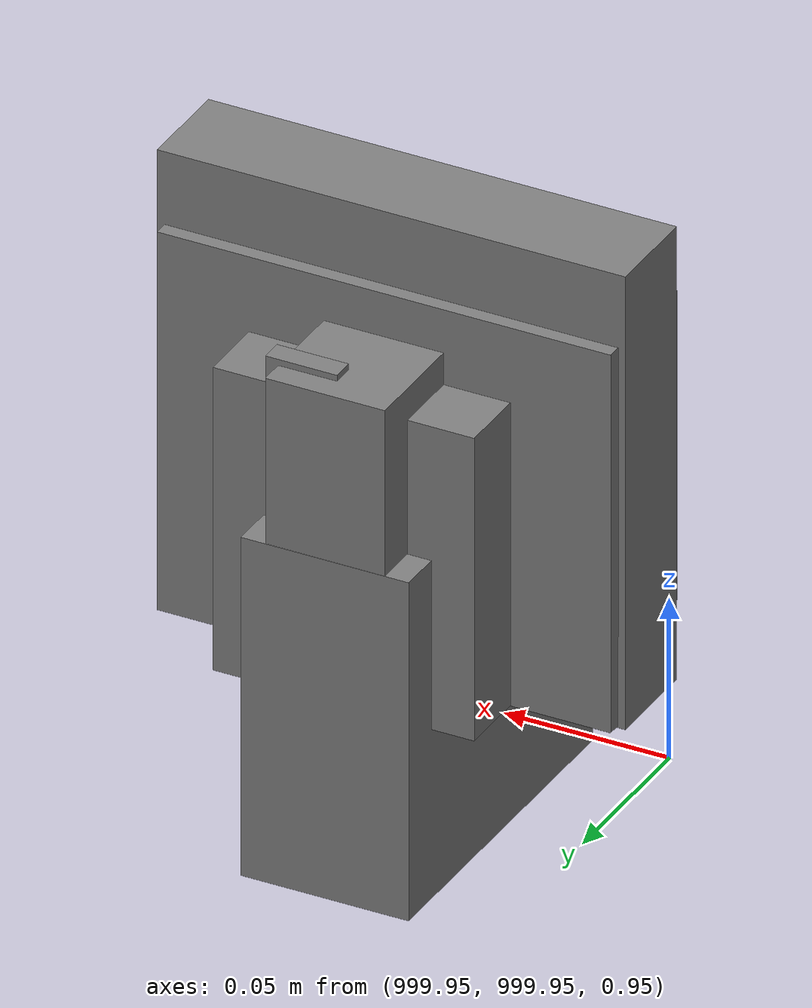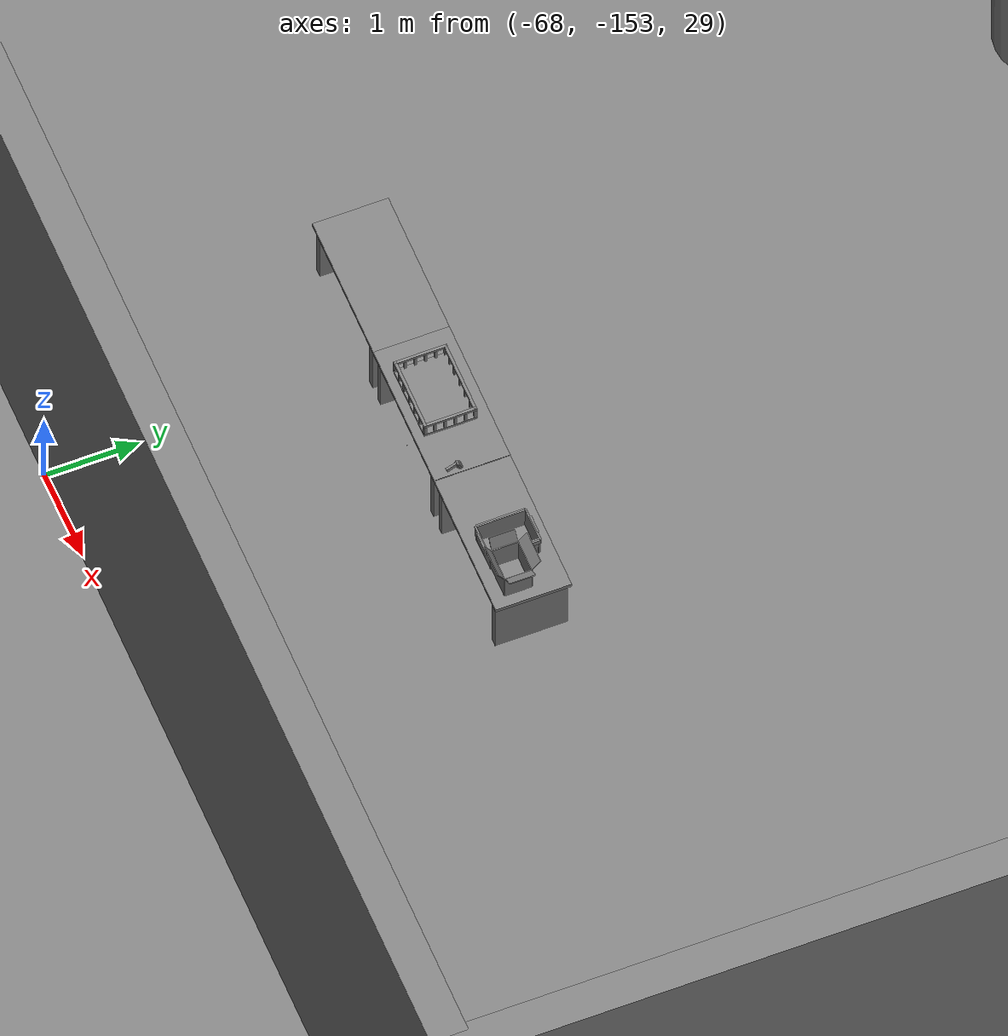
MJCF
<mujoco>
    <option gravity="0.000000000 0.000000000 -9.810000420" timestep="0.0049999999" integrator="implicitfast" density="1.225" viscosity="1.8000001e-05" noslip_iterations="10" iterations="100" sdf_iterations="50">
        <flag multiccd="disable"/>
    </option>
    <size memory="1000M"/>
    <compiler coordinate="local"/>
    <worldbody>
        <light cutoff="30" pos="0 1 1" dir="0 -1 -2"/>
        <light cutoff="30" pos="0 -1 1" dir="0 1 -2"/>
        <body pos="-66.158691406 -149.470977783 31.164209366" euler="-71.055076599 80.898002625 51.154441833" mocap="true" name="spotlight1_SpotLight"/>
        <body pos="1000.000000000 1000.000000000 1.000000000" euler="0.000011953 0.000005123 -179.999984741" name="openloong_gripper_2f85_fix_base_usda_intel_box">
            <geom contype="1" conaffinity="1" density="1000" type="box" material="" rgba="0.500000000 0.500000000 0.500000000 1.000000000" solimp="0.899999976 0.949999988 0.001000000" friction="1.000000000 0.005000000 0.000100000" solref="0.020000000 1.000000000" margin="0" condim="3" group="0" pos="0.000000000 -0.000067139 0.000082284" quat="0.707106709 0.000000225 0.000000253 0.707106650" size="0.052800003 0.025300000 0.052800003" name="openloong_gripper_2f85_fix_base_usda_geom_666EA14B_9941_4F8F_A904_D6A9CDBD7EA2"/>
            <freejoint name="openloong_gripper_2f85_fix_base_usda_intel_box_joint"/>
            <site size="0.005000000 0.005000000 0.005000000" rgba="0.500000000 0.500000000 0.500000000 1.000000000" pos="0.000000000 0.000000000 0.000000000" quat="0.999961913 0.008726500 0.000000000 0.000000000" group="0" type="sphere" name="openloong_gripper_2f85_fix_base_usda_intel_boxsite"/>
        </body>
        <body pos="1000.000000000 999.999938965 1.000000000" euler="0.000000000 0.000000000 180.000000000" name="openloong_gripper_2f85_fix_base_usda_intelcore_i5">
            <geom contype="1" conaffinity="1" density="1000" type="box" material="" rgba="0.500000000 0.500000000 0.500000000 1.000000000" solimp="0.899999976 0.949999988 0.001000000" friction="1.000000000 0.005000000 0.000100000" solref="0.020000000 1.000000000" margin="0" condim="3" group="0" pos="0.000000000 0.000000000 0.051722717" quat="0.707106709 0.000000000 0.000000000 -0.707106769" size="0.052800000 0.018080002 0.052800000" name="openloong_gripper_2f85_fix_base_usda_geom_04FB1E32_3718_457E_AEA7_696B2F777C3D"/>
            <freejoint name="openloong_gripper_2f85_fix_base_usda_intelcore_i5_joint"/>
            <site size="0.005000000 0.005000000 0.005000000" rgba="0.500000000 0.500000000 0.500000000 1.000000000" pos="0.000000000 0.000000000 0.000000000" quat="0.999961913 0.008726534 0.000000000 0.000000000" group="0" type="sphere" name="openloong_gripper_2f85_fix_base_usda_intelcore_i5site"/>
        </body>
        <body pos="-66.004989624 -149.776748657 31.163509369" euler="157.279968262 -75.112579346 -30.941188812" mocap="true" name="spotlight6_SpotLight"/>
        <body pos="1000.000000000 1000.000000000 1.000000000" euler="0.000000000 0.000000000 180.000000000" name="openloong_gripper_2f85_fix_base_usda_wifi_box">
            <geom contype="1" conaffinity="1" density="1000" type="box" material="" rgba="0.500000000 0.500000000 0.500000000 1.000000000" solimp="0.899999976 0.949999988 0.001000000" friction="1.000000000 0.005000000 0.000100000" solref="0.020000000 1.000000000" margin="0" condim="3" group="0" pos="0.000000000 0.000000000 0.058978677" quat="0.000000000 0.000000047 0.000000000 1.000000000" size="0.068499997 0.018999999 0.059000000" name="openloong_gripper_2f85_fix_base_usda_geom_94BA88D6_779F_42B4_AF59_938E717D8DC1"/>
            <freejoint name="openloong_gripper_2f85_fix_base_usda_wifi_box_joint"/>
            <site size="0.005000000 0.005000000 0.005000000" rgba="0.500000000 0.500000000 0.500000000 1.000000000" pos="0.000000000 0.000000000 0.000000000" quat="0.999961913 0.008726500 0.000000000 0.000000000" group="0" type="sphere" name="openloong_gripper_2f85_fix_base_usda_wifi_boxsite"/>
        </body>
        <body pos="1000.000000000 1000.000000000 1.000000000" euler="0.000000000 0.000000000 180.000000000" name="openloong_gripper_2f85_fix_base_usda_cpu_fan">
            <geom contype="1" conaffinity="1" density="1000" type="box" material="" rgba="0.500000000 0.500000000 0.500000000 1.000000000" solimp="0.899999976 0.949999988 0.001000000" friction="1.000000000 0.005000000 0.000100000" solref="0.020000000 1.000000000" margin="0" condim="3" group="0" pos="0.000000000 0.000000000 0.070034981" quat="0.000000000 0.000000000 0.000000000 1.000000000" size="0.070700005 0.014699999 0.070700005" name="openloong_gripper_2f85_fix_base_usda_geom_722507E5_7841_448B_9B02_6BE1762650DE"/>
            <freejoint name="openloong_gripper_2f85_fix_base_usda_cpu_fan_joint"/>
            <site size="0.005000000 0.005000000 0.005000000" rgba="0.500000000 0.500000000 0.500000000 1.000000000" pos="0.000000000 0.000000000 0.000000000" quat="0.999961913 0.008726535 0.000000000 0.000000000" group="0" type="sphere" name="openloong_gripper_2f85_fix_base_usda_cpu_fancsite"/>
        </body>
        <body pos="1000.000000000 1000.000000000 1.000000000" euler="0.000000000 0.000000000 180.000000000" name="openloong_gripper_2f85_fix_base_usda_battery_01">
            <geom contype="1" conaffinity="1" density="1000" type="box" material="" rgba="0.500000000 0.500000000 0.500000000 1.000000000" solimp="0.899999976 0.949999988 0.001000000" friction="1.000000000 0.005000000 0.000100000" solref="0.020000000 1.000000000" margin="0" condim="3" group="0" pos="-0.011123657 -0.041940309 0.101691343" quat="1.000000000 0.000000000 0.000000000 0.000000000" size="0.010800000 0.003375000 0.004725000" name="openloong_gripper_2f85_fix_base_usda_geom_4DF90F9C_8FF6_4FCB_BF9D_228CFFD1E40A"/>
            <geom contype="1" conaffinity="1" density="1000" type="box" material="" rgba="0.500000000 0.500000000 0.500000000 1.000000000" solimp="0.899999976 0.949999988 0.001000000" friction="1.000000000 0.005000000 0.000100000" solref="0.020000000 1.000000000" margin="0" condim="3" group="0" pos="-0.010876465 -0.044247437 0.047066893" quat="0.998702705 -0.050920475 0.000000000 0.000000000" size="0.009450001 0.002700000 0.024975000" name="openloong_gripper_2f85_fix_base_usda_geom_264659C2_C54B_4650_B4E3_7CEEAAE9F577"/>
            <geom contype="1" conaffinity="1" density="1000" type="box" material="" rgba="0.500000000 0.500000000 0.500000000 1.000000000" solimp="0.899999976 0.949999988 0.001000000" friction="1.000000000 0.005000000 0.000100000" solref="0.020000000 1.000000000" margin="0" condim="3" group="0" pos="-0.001235962 -0.000659180 0.047381196" quat="1.000000000 0.000000000 0.000000000 0.000000000" size="0.039420001 0.039150000 0.047250003" name="openloong_gripper_2f85_fix_base_usda_geom_CD23F558_8FD9_4444_A0CE_4E2FBCBDA563"/>
            <geom contype="1" conaffinity="1" density="1000" type="box" material="" rgba="0.500000000 0.500000000 0.500000000 1.000000000" solimp="0.899999976 0.949999988 0.001000000" friction="1.000000000 0.005000000 0.000100000" solref="0.020000000 1.000000000" margin="0" condim="3" group="0" pos="-0.010876465 -0.039138794 0.009851727" quat="1.000000000 0.000000000 0.000000000 0.000000000" size="0.009450001 0.010800000 0.013500000" name="openloong_gripper_2f85_fix_base_usda_geom_7E7AAE26_9CED_4686_B940_04F9C973E7AE"/>
            <geom contype="1" conaffinity="1" density="1000" type="box" material="" rgba="0.500000000 0.500000000 0.500000000 1.000000000" solimp="0.899999976 0.949999988 0.001000000" friction="1.000000000 0.005000000 0.000100000" solref="0.020000000 1.000000000" margin="0" condim="3" group="0" pos="-0.010876465 -0.041528322 0.071508206" quat="1.000000000 0.000000000 0.000000000 0.000000000" size="0.009450001 0.002700000 0.027000001" name="openloong_gripper_2f85_fix_base_usda_geom_C4CC7A23_F83A_466C_8C62_7D8D0CD58A99"/>
            <freejoint name="openloong_gripper_2f85_fix_base_usda_battery_01_joint"/>
            <site size="0.005000000 0.005000000 0.005000000" rgba="0.500000000 0.500000000 0.500000000 1.000000000" pos="0.000000000 0.000000000 0.000000000" quat="0.999961913 0.008726500 0.000000000 0.000000000" group="0" type="sphere" name="openloong_gripper_2f85_fix_base_usda_battery_01site"/>
        </body>
        <body pos="-66.167030334 -149.575042725 31.165349960" euler="-20.506059647 26.558179855 70.261390686" mocap="true" name="spotlight4_SpotLight"/>
        <body pos="-64.866622925 -149.383972168 30.183746338" euler="89.999984741 89.999946594 0.000000000" name="openloong_gripper_2f85_fix_base_usda_bluebox_01">
            <geom contype="1" conaffinity="1" density="1000" type="box" material="" rgba="0.500000000 0.500000000 0.500000000 1.000000000" solimp="0.899999976 0.949999988 0.001000000" friction="1.000000000 0.005000000 0.000100000" solref="0.020000000 1.000000000" margin="0" condim="3" group="0" pos="0.276580811 0.187225342 0.000068665" quat="0.707106948 0.000077471 0.707106352 0.000077486" size="0.100000001 0.057999998 0.010000000" name="openloong_gripper_2f85_fix_base_usda_geom_D84919B5_AEE3_4DF5_A287_C94A1D372CCB"/>
            <geom contype="1" conaffinity="1" density="1000" type="box" material="" rgba="0.500000000 0.500000000 0.500000000 1.000000000" solimp="0.899999976 0.949999988 0.001000000" friction="1.000000000 0.005000000 0.000100000" solref="0.020000000 1.000000000" margin="0" condim="3" group="0" pos="0.000000000 0.002883911 0.000000000" quat="0.999999881 0.000000000 0.000000000 0.000000000" size="0.254000008 0.003000000 0.172000006" name="openloong_gripper_2f85_fix_base_usda_geom_22534AD0_7BD7_4DB6_A3EF_C40866C56E24"/>
            <geom contype="1" conaffinity="1" density="1000" type="box" material="" rgba="0.500000000 0.500000000 0.500000000 1.000000000" solimp="0.899999976 0.949999988 0.001000000" friction="1.000000000 0.005000000 0.000100000" solref="0.020000000 1.000000000" margin="0" condim="3" group="0" pos="0.000000000 0.124874115 0.173484802" quat="0.999796331 0.020176515 -0.000000015 0.000000030" size="0.259999990 0.119999997 0.007000000" name="openloong_gripper_2f85_fix_base_usda_geom_E25CD7DD_23DD_412A_BD3A_6ECD929F6757"/>
            <geom contype="1" conaffinity="1" density="1000" type="box" material="" rgba="0.500000000 0.500000000 0.500000000 1.000000000" solimp="0.899999976 0.949999988 0.001000000" friction="1.000000000 0.005000000 0.000100000" solref="0.020000000 1.000000000" margin="0" condim="3" group="0" pos="0.000000000 0.124874115 -0.173469543" quat="0.999796331 -0.020176545 -0.000000015 0.000000000" size="0.259999990 0.119999997 0.007000000" name="openloong_gripper_2f85_fix_base_usda_geom_597CECE8_8783_4AF4_9005_796AAC8AE238"/>
            <geom contype="1" conaffinity="1" density="1000" type="box" material="" rgba="0.500000000 0.500000000 0.500000000 1.000000000" solimp="0.899999976 0.949999988 0.001000000" friction="1.000000000 0.005000000 0.000100000" solref="0.020000000 1.000000000" margin="0" condim="3" group="0" pos="0.000000000 0.214008331 0.188980103" quat="0.999912977 0.013176724 0.000000015 0.000000000" size="0.259999990 0.029999999 0.012500000" name="openloong_gripper_2f85_fix_base_usda_geom_44410362_1DF1_43DF_B7EE_F58BE8F699F1"/>
            <geom contype="1" conaffinity="1" density="1000" type="box" material="" rgba="0.500000000 0.500000000 0.500000000 1.000000000" solimp="0.899999976 0.949999988 0.001000000" friction="1.000000000 0.005000000 0.000100000" solref="0.020000000 1.000000000" margin="0" condim="3" group="0" pos="-0.258361816 0.125289917 0.001876831" quat="0.702796936 -0.020792112 0.710783124 0.020769298" size="0.189999998 0.119999997 0.009000000" name="openloong_gripper_2f85_fix_base_usda_geom_70620B38_15BA_4B0C_AA55_799736116F25"/>
            <geom contype="1" conaffinity="1" density="1000" type="box" material="" rgba="0.500000000 0.500000000 0.500000000 1.000000000" solimp="0.899999976 0.949999988 0.001000000" friction="1.000000000 0.005000000 0.000100000" solref="0.020000000 1.000000000" margin="0" condim="3" group="0" pos="0.000000000 0.214008331 -0.188980103" quat="0.999912977 -0.013176769 0.000000030 0.000000015" size="0.259999990 0.029999999 0.012500000" name="openloong_gripper_2f85_fix_base_usda_geom_1155E2FE_4C4A_4EAB_8865_9291BD173AE1"/>
            <geom contype="1" conaffinity="1" density="1000" type="box" material="" rgba="0.500000000 0.500000000 0.500000000 1.000000000" solimp="0.899999976 0.949999988 0.001000000" friction="1.000000000 0.005000000 0.000100000" solref="0.020000000 1.000000000" margin="0" condim="3" group="0" pos="-0.276611328 0.187225342 0.000068665" quat="0.707106650 0.000077441 0.707106709 0.000077456" size="0.100000001 0.057999998 0.010000000" name="openloong_gripper_2f85_fix_base_usda_geom_DA89E299_F2C4_4416_B72E_0BD8FE3026EF"/>
            <geom contype="1" conaffinity="1" density="1000" type="box" material="" rgba="0.500000000 0.500000000 0.500000000 1.000000000" solimp="0.899999976 0.949999988 0.001000000" friction="1.000000000 0.005000000 0.000100000" solref="0.020000000 1.000000000" margin="0" condim="3" group="0" pos="0.258331299 0.125289917 0.001876831" quat="0.702851415 0.018856421 0.710823774 -0.019329369" size="0.189999998 0.119999997 0.009000000" name="openloong_gripper_2f85_fix_base_usda_geom_F777C97F_8DA0_40D5_B431_6E749454B97D"/>
            <freejoint name="openloong_gripper_2f85_fix_base_usda_bluebox_01_joint"/>
            <site size="0.005000000 0.005000000 0.005000000" rgba="0.500000000 0.500000000 0.500000000 1.000000000" pos="0.000000000 0.000000000 0.000000000" quat="0.999961913 0.008726534 0.000000000 0.000000000" group="0" type="sphere" name="openloong_gripper_2f85_fix_base_usda_bluebox_01site"/>
        </body>
        <body pos="-64.496299744 -149.491867065 30.235729218" euler="0.000000000 0.000000000 89.999946594" name="openloong_gripper_2f85_fix_base_usda_cardboardbox_01">
            <geom contype="1" conaffinity="1" density="1000" type="box" material="" rgba="0.500000000 0.500000000 0.500000000 1.000000000" solimp="0.899999976 0.949999988 0.001000000" friction="1.000000000 0.005000000 0.000100000" solref="0.020000000 1.000000000" margin="0" condim="3" group="0" pos="-0.003166199 -0.004086494 0.005052090" quat="1.000000000 0.000000000 0.000000000 0.000000000" size="0.142499998 0.177500010 0.005000000" name="openloong_gripper_2f85_fix_base_usda_geom_838E12DD_D9A1_4D74_8D61_0AD5ADFDF13B"/>
            <geom contype="1" conaffinity="1" density="1000" type="box" material="" rgba="0.500000000 0.500000000 0.500000000 1.000000000" solimp="0.899999976 0.949999988 0.001000000" friction="1.000000000 0.005000000 0.000100000" solref="0.020000000 1.000000000" margin="0" condim="3" group="0" pos="-0.003166199 0.170316696 0.150570869" quat="1.000000000 0.000000000 0.000000000 0.000000000" size="0.142499998 0.005000000 0.149999991" name="openloong_gripper_2f85_fix_base_usda_geom_E2586068_0F26_4AF8_A2DD_D5992332337A"/>
            <geom contype="1" conaffinity="1" density="1000" type="box" material="" rgba="0.500000000 0.500000000 0.500000000 1.000000000" solimp="0.899999976 0.949999988 0.001000000" friction="1.000000000 0.005000000 0.000100000" solref="0.020000000 1.000000000" margin="0" condim="3" group="0" pos="-0.147399902 -0.005307198 0.150570869" quat="1.000000000 0.000000000 0.000000000 0.000000000" size="0.005000000 0.177500010 0.149999991" name="openloong_gripper_2f85_fix_base_usda_geom_91901C6C_42A2_4782_926B_2CB6A5EE4964"/>
            <geom contype="1" conaffinity="1" density="1000" type="box" material="" rgba="0.500000000 0.500000000 0.500000000 1.000000000" solimp="0.899999976 0.949999988 0.001000000" friction="1.000000000 0.005000000 0.000100000" solref="0.020000000 1.000000000" margin="0" condim="3" group="0" pos="0.140275955 -0.005307198 0.150570869" quat="1.000000000 0.000000000 0.000000000 0.000000000" size="0.005000000 0.177500010 0.149999991" name="openloong_gripper_2f85_fix_base_usda_geom_72878CE7_A9D4_4A23_8BAD_4DB4B1A3E382"/>
            <geom contype="1" conaffinity="1" density="1000" type="box" material="" rgba="0.500000000 0.500000000 0.500000000 1.000000000" solimp="0.899999976 0.949999988 0.001000000" friction="1.000000000 0.005000000 0.000100000" solref="0.020000000 1.000000000" margin="0" condim="3" group="0" pos="-0.003166199 -0.181550980 0.150570869" quat="1.000000000 0.000000000 0.000000000 0.000000000" size="0.142499998 0.005000000 0.149999991" name="openloong_gripper_2f85_fix_base_usda_geom_447B3001_4106_4F9A_B7D2_F0622524743F"/>
            <freejoint name="openloong_gripper_2f85_fix_base_usda_cardboardbox_01_joint"/>
            <site size="0.005000000 0.005000000 0.005000000" rgba="0.500000000 0.500000000 0.500000000 1.000000000" pos="0.000000000 0.000000000 0.000000000" quat="0.999961913 0.008726535 0.000000000 0.000000000" group="0" type="sphere" name="openloong_gripper_2f85_fix_base_usda_site_849DA75F_162B_444B_98F4_5AB77EB1907F"/>
            <body pos="0.139160156 -0.004048347 0.301930904" euler="-179.999954224 49.383502960 179.999954224" name="openloong_gripper_2f85_fix_base_usda_A1_006">
                <geom contype="1" conaffinity="1" density="1000" type="box" material="" rgba="0.500000000 0.500000000 0.500000000 1.000000000" solimp="0.899999976 0.949999988 0.001000000" friction="1.000000000 0.005000000 0.000100000" solref="0.020000000 1.000000000" margin="0" condim="3" group="0" pos="-0.071587563 0.000009537 0.001745224" quat="0.999999881 0.000000000 0.000000000 0.000000000" size="0.071249999 0.179999992 0.002500000" name="openloong_gripper_2f85_fix_base_usda_geom_C7EEB5E5_18EC_4C81_8CEE_EAD8E6EFA4BE"/>
                <joint armature="0" stiffness="0.07" damping="0.0099999998" axis="0.000000 1.000000 0.000000" type="hinge" name="openloong_gripper_2f85_fix_base_usda_A1_006"/>
            </body>
            <body pos="-0.145902634 -0.004086494 0.301938057" euler="-180.000000000 -60.000011444 -180.000000000" name="openloong_gripper_2f85_fix_base_usda_A2_006">
                <geom contype="1" conaffinity="1" density="1000" type="box" material="" rgba="0.500000000 0.500000000 0.500000000 1.000000000" solimp="0.899999976 0.949999988 0.001000000" friction="1.000000000 0.005000000 0.000100000" solref="0.020000000 1.000000000" margin="0" condim="3" group="0" pos="0.071268082 0.000009537 0.002717972" quat="0.000002921 0.000000000 -0.000000030 0.999999881" size="0.071249999 0.179999992 0.002500000" name="openloong_gripper_2f85_fix_base_usda_geom_6D5238D2_8089_4799_9A5B_3E682F60E3AA"/>
                <joint armature="0" stiffness="0.07" damping="0.0099999998" axis="0.000000 1.000000 0.000000" type="hinge" name="openloong_gripper_2f85_fix_base_usda_A2_006"/>
            </body>
            <body pos="-0.003385544 0.175991058 0.301930904" euler="-125.858116150 -0.000004561 0.000002331" name="openloong_gripper_2f85_fix_base_usda_B2_006">
                <geom contype="1" conaffinity="1" density="1000" type="box" material="" rgba="0.500000000 0.500000000 0.500000000 1.000000000" solimp="0.899999976 0.949999988 0.001000000" friction="1.000000000 0.005000000 0.000100000" solref="0.020000000 1.000000000" margin="0" condim="3" group="0" pos="0.000009537 -0.070939064 -0.002470016" quat="0.999614120 0.027776197 -0.000000015 0.000000030" size="0.137500003 0.064999998 0.005000000" name="openloong_gripper_2f85_fix_base_usda_geom_AE1120F5_0500_414D_A65C_A1620F32DD55"/>
                <joint armature="0" stiffness="0.07" damping="0.0099999998" axis="1.000000 0.000000 0.000000" type="hinge" name="openloong_gripper_2f85_fix_base_usda_B2_006"/>
            </body>
            <body pos="-0.003385544 -0.184140205 0.301938057" euler="147.805557251 0.000000000 0.000000000" name="openloong_gripper_2f85_fix_base_usda_B1_006">
                <geom contype="1" conaffinity="1" density="1000" type="box" material="" rgba="0.500000000 0.500000000 0.500000000 1.000000000" solimp="0.899999976 0.949999988 0.001000000" friction="1.000000000 0.005000000 0.000100000" solref="0.020000000 1.000000000" margin="0" condim="3" group="0" pos="-0.000028610 0.070202351 -0.002703667" quat="0.999614179 -0.027776167 0.000000000 0.000000000" size="0.137500003 0.064999998 0.005000000" name="openloong_gripper_2f85_fix_base_usda_geom_B18C0F20_948F_49A7_8FD2_FD746C193C80"/>
                <joint armature="0" stiffness="0.07" damping="0.0099999998" axis="1.000000 0.000000 0.000000" type="hinge" name="openloong_gripper_2f85_fix_base_usda_B1_006"/>
            </body>
        </body>
        <body pos="-65.882858276 -149.481979370 30.229999542" euler="-64.487716675 0.000000000 0.000000000" name="openloong_gripper_2f85_fix_base_usda_Barcode">
            <geom contype="1" conaffinity="1" density="1000" type="box" material="" rgba="0.500000000 0.500000000 0.500000000 1.000000000" solimp="0.899999976 0.949999988 0.001000000" friction="1.000000000 0.005000000 0.000100000" solref="0.020000000 1.000000000" margin="0" condim="3" group="0" pos="0.000000000 0.013038635 0.001419067" quat="0.000000000 0.000000000 0.000000000 1.000000119" size="0.034000002 0.010000000 0.017999999" name="openloong_gripper_2f85_fix_base_usda_geom_205ABE4E_2E9E_44E2_9FAC_BD083203507F"/>
            <geom contype="1" conaffinity="1" density="1000" type="box" material="" rgba="0.500000000 0.500000000 0.500000000 1.000000000" solimp="0.899999976 0.949999988 0.001000000" friction="1.000000000 0.005000000 0.000100000" solref="0.020000000 1.000000000" margin="0" condim="3" group="0" pos="0.000000000 -0.035301208 -0.007095337" quat="0.000000000 0.000000000 -0.043619365 0.999048233" size="0.028999999 0.010000000 0.020000000" name="openloong_gripper_2f85_fix_base_usda_geom_803940E6_10B1_447A_BF64_92B9AAE51676"/>
            <geom contype="1" conaffinity="1" density="1000" type="box" material="" rgba="0.500000000 0.500000000 0.500000000 1.000000000" solimp="0.899999976 0.949999988 0.001000000" friction="1.000000000 0.005000000 0.000100000" solref="0.020000000 1.000000000" margin="0" condim="3" group="0" pos="0.000000000 -0.043411255 -0.011749268" quat="0.922262907 0.386563420 0.000000000 0.000000000" size="0.026000001 0.010000000 0.020000000" name="openloong_gripper_2f85_fix_base_usda_geom_E524BBD0_8F39_48F6_AC59_67C028AB5E78"/>
            <geom contype="1" conaffinity="1" density="1000" type="box" material="" rgba="0.500000000 0.500000000 0.500000000 1.000000000" solimp="0.899999976 0.949999988 0.001000000" friction="1.000000000 0.005000000 0.000100000" solref="0.020000000 1.000000000" margin="0" condim="3" group="0" pos="0.000000000 -0.016967773 -0.031860352" quat="0.000000000 0.000000000 0.000000000 1.000000119" size="0.008000000 0.010000000 0.013000000" name="openloong_gripper_2f85_fix_base_usda_geom_DCA4C822_8C88_4C71_BEC7_AF3077EAC671"/>
            <geom contype="1" conaffinity="1" density="1000" type="box" material="" rgba="0.500000000 0.500000000 0.500000000 1.000000000" solimp="0.899999976 0.949999988 0.001000000" friction="1.000000000 0.005000000 0.000100000" solref="0.020000000 1.000000000" margin="0" condim="3" group="0" pos="0.000000000 -0.001869202 0.000312805" quat="0.953716993 0.300705761 0.000000000 0.000000000" size="0.032000002 0.010000000 0.018999999" name="openloong_gripper_2f85_fix_base_usda_geom_BC5534E7_B80E_44D7_96F5_419D3740CEE7"/>
            <geom contype="1" conaffinity="1" density="1000" type="box" material="" rgba="0.500000000 0.500000000 0.500000000 1.000000000" solimp="0.899999976 0.949999988 0.001000000" friction="1.000000000 0.005000000 0.000100000" solref="0.020000000 1.000000000" margin="0" condim="3" group="0" pos="0.000000000 -0.019531250 -0.003173828" quat="0.953716993 0.300705761 0.000000000 0.000000000" size="0.030999999 0.010000000 0.020000000" name="openloong_gripper_2f85_fix_base_usda_geom_42E5895B_3375_4053_9C31_E84D4A821510"/>
            <geom contype="1" conaffinity="1" density="1000" type="box" material="" rgba="0.500000000 0.500000000 0.500000000 1.000000000" solimp="0.899999976 0.949999988 0.001000000" friction="1.000000000 0.005000000 0.000100000" solref="0.020000000 1.000000000" margin="0" condim="3" group="0" pos="0.000000000 -0.035301208 -0.007095337" quat="0.953716993 0.300705761 0.000000000 0.000000000" size="0.028999999 0.010000000 0.020000000" name="openloong_gripper_2f85_fix_base_usda_geom_26518814_E4FA_4B0B_8F4D_2D6A2BB0BC1A"/>
            <geom contype="1" conaffinity="1" density="1000" type="box" material="" rgba="0.500000000 0.500000000 0.500000000 1.000000000" solimp="0.899999976 0.949999988 0.001000000" friction="1.000000000 0.005000000 0.000100000" solref="0.020000000 1.000000000" margin="0" condim="3" group="0" pos="0.000000000 -0.042617798 -0.071121216" quat="0.000000000 0.000000000 0.000000000 1.000000119" size="0.013000000 0.021000000 0.059999999" name="openloong_gripper_2f85_fix_base_usda_geom_043BD730_FCD5_42A9_8939_732A3B08D74F"/>
            <freejoint name="openloong_gripper_2f85_fix_base_usda_Barcode_joint"/>
            <site size="0.005000000 0.005000000 0.005000000" rgba="0.500000000 0.500000000 0.500000000 1.000000000" pos="0.000000000 0.000000000 0.000000000" quat="1.000000000 0.000000000 0.000000000 0.000000000" group="0" type="sphere" name="openloong_gripper_2f85_fix_base_usda_Barcode_site"/>
        </body>
        <body pos="-66.745018005 -149.392349243 30.184000015" euler="0.000000000 0.000000000 89.999946594" name="[22331112853328]_Basket_01">
            <geom contype="1" conaffinity="1" density="1000" type="box" material="" rgba="0.500000000 0.500000000 0.500000000 1.000000000" solimp="0.899999976 0.949999988 0.001000000" friction="1.000000000 0.005000000 0.000100000" solref="0.020000000 1.000000000" margin="0" condim="3" group="0" pos="-0.052425385 0.389207840 0.089787483" quat="0.707107008 0.000000000 0.000000000 0.707106411" size="0.014249999 0.014249999 0.059999999" name="[22331112853328]_geom_F1ABC099_34B4_4A80_BDE0_10CFFBFE28FF"/>
            <geom contype="1" conaffinity="1" density="1000" type="box" material="" rgba="0.500000000 0.500000000 0.500000000 1.000000000" solimp="0.899999976 0.949999988 0.001000000" friction="1.000000000 0.005000000 0.000100000" solref="0.020000000 1.000000000" margin="0" condim="3" group="0" pos="0.264015198 -0.133043289 0.089787483" quat="0.707107008 0.000000000 0.000000000 0.707106411" size="0.014249999 0.014249999 0.059999999" name="[22331112853328]_geom_BE3C48B8_A828_4D92_B644_AB88493551C4"/>
            <geom contype="1" conaffinity="1" density="1000" type="box" material="" rgba="0.500000000 0.500000000 0.500000000 1.000000000" solimp="0.899999976 0.949999988 0.001000000" friction="1.000000000 0.005000000 0.000100000" solref="0.020000000 1.000000000" margin="0" condim="3" group="0" pos="-0.264015198 -0.265548706 0.089793205" quat="0.707107008 0.000000000 0.000000000 0.707106411" size="0.014249999 0.014249999 0.059999999" name="[22331112853328]_geom_EB494835_ED2E_45AB_9693_040B15AD71FD"/>
            <geom contype="1" conaffinity="1" density="1000" type="box" material="" rgba="0.500000000 0.500000000 0.500000000 1.000000000" solimp="0.899999976 0.949999988 0.001000000" friction="1.000000000 0.005000000 0.000100000" solref="0.020000000 1.000000000" margin="0" condim="3" group="0" pos="-0.160263062 -0.389322281 0.089793205" quat="0.707107008 0.000000000 0.000000000 0.707106411" size="0.014249999 0.014249999 0.059999999" name="[22331112853328]_geom_2D7B6AAA_D46E_4190_9617_7C359EB05747"/>
            <geom contype="1" conaffinity="1" density="1000" type="box" material="" rgba="0.500000000 0.500000000 0.500000000 1.000000000" solimp="0.899999976 0.949999988 0.001000000" friction="1.000000000 0.005000000 0.000100000" solref="0.020000000 1.000000000" margin="0" condim="3" group="0" pos="0.162265778 -0.389322281 0.089787483" quat="0.707107008 0.000000000 0.000000000 0.707106411" size="0.014249999 0.014249999 0.059999999" name="[22331112853328]_geom_793437C1_0571_465A_A9DD_593369C58A5C"/>
            <geom contype="1" conaffinity="1" density="1000" type="box" material="" rgba="0.500000000 0.500000000 0.500000000 1.000000000" solimp="0.899999976 0.949999988 0.001000000" friction="1.000000000 0.005000000 0.000100000" solref="0.020000000 1.000000000" margin="0" condim="3" group="0" pos="0.264015198 0.389207840 0.089787483" quat="0.707107008 0.000000000 0.000000000 0.707106411" size="0.014249999 0.014249999 0.059999999" name="[22331112853328]_geom_D72D1EE3_CD91_460A_9729_CD4C9E43CC1D"/>
            <geom contype="1" conaffinity="1" density="1000" type="box" material="" rgba="0.500000000 0.500000000 0.500000000 1.000000000" solimp="0.899999976 0.949999988 0.001000000" friction="1.000000000 0.005000000 0.000100000" solref="0.020000000 1.000000000" margin="0" condim="3" group="0" pos="-0.264015198 -0.133043289 0.089793205" quat="0.707107008 0.000000000 0.000000000 0.707106411" size="0.014249999 0.014249999 0.059999999" name="[22331112853328]_geom_011982AB_BEF5_405E_B76D_48369D5446C0"/>
            <geom contype="1" conaffinity="1" density="1000" type="box" material="" rgba="0.500000000 0.500000000 0.500000000 1.000000000" solimp="0.899999976 0.949999988 0.001000000" friction="1.000000000 0.005000000 0.000100000" solref="0.020000000 1.000000000" margin="0" condim="3" group="0" pos="-0.264026642 0.269256592 0.089793205" quat="0.707107008 0.000000000 0.000000000 0.707106411" size="0.014249999 0.014249999 0.059999999" name="[22331112853328]_geom_9BC6C131_FCFA_41D5_AA6B_5BECD75C0484"/>
            <geom contype="1" conaffinity="1" density="1000" type="box" material="" rgba="0.500000000 0.500000000 0.500000000 1.000000000" solimp="0.899999976 0.949999988 0.001000000" friction="1.000000000 0.005000000 0.000100000" solref="0.020000000 1.000000000" margin="0" condim="3" group="0" pos="0.054462433 0.389207840 0.089787483" quat="0.707107008 0.000000000 0.000000000 0.707106411" size="0.014249999 0.014249999 0.059999999" name="[22331112853328]_geom_42D9BE7F_36DB_4C3D_A8FF_4BF5105CD5F7"/>
            <geom contype="1" conaffinity="1" density="1000" type="box" material="" rgba="0.500000000 0.500000000 0.500000000 1.000000000" solimp="0.899999976 0.949999988 0.001000000" friction="1.000000000 0.005000000 0.000100000" solref="0.020000000 1.000000000" margin="0" condim="3" group="0" pos="0.054462433 -0.389322281 0.089787483" quat="0.707107008 0.000000000 0.000000000 0.707106411" size="0.014249999 0.014249999 0.059999999" name="[22331112853328]_geom_D37C4A26_90FA_4ED5_B0C5_F3776C17C5C5"/>
            <geom contype="1" conaffinity="1" density="1000" type="box" material="" rgba="0.500000000 0.500000000 0.500000000 1.000000000" solimp="0.899999976 0.949999988 0.001000000" friction="1.000000000 0.005000000 0.000100000" solref="0.020000000 1.000000000" margin="0" condim="3" group="0" pos="0.264015198 0.269256592 0.089793205" quat="0.707107008 0.000000000 0.000000000 0.707106411" size="0.014249999 0.014249999 0.059999999" name="[22331112853328]_geom_B14DEA5F_DB91_40AB_B520_585B69623758"/>
            <geom contype="1" conaffinity="1" density="1000" type="box" material="" rgba="0.500000000 0.500000000 0.500000000 1.000000000" solimp="0.899999976 0.949999988 0.001000000" friction="1.000000000 0.005000000 0.000100000" solref="0.020000000 1.000000000" margin="0" condim="3" group="0" pos="0.264015198 -0.389322281 0.089787483" quat="0.707107008 0.000000000 0.000000000 0.707106411" size="0.014249999 0.014249999 0.059999999" name="[22331112853328]_geom_444C3751_7EC3_4B29_B252_B48A768B8A7C"/>
            <geom contype="1" conaffinity="1" density="1000" type="box" material="" rgba="0.500000000 0.500000000 0.500000000 1.000000000" solimp="0.899999976 0.949999988 0.001000000" friction="1.000000000 0.005000000 0.000100000" solref="0.020000000 1.000000000" margin="0" condim="3" group="0" pos="0.000000000 0.000000000 0.015998840" quat="0.707107008 0.000000000 0.000000000 0.707106411" size="0.403499991 0.279000014 0.015750000" name="[22331112853328]_geom_5EED3BC2_F9A7_47CC_A77B_AF5AFF35568C"/>
            <geom contype="1" conaffinity="1" density="1000" type="box" material="" rgba="0.500000000 0.500000000 0.500000000 1.000000000" solimp="0.899999976 0.949999988 0.001000000" friction="1.000000000 0.005000000 0.000100000" solref="0.020000000 1.000000000" margin="0" condim="3" group="0" pos="0.000000000 -0.389476776 0.163619041" quat="0.707107008 0.000000000 0.000000000 0.707106411" size="0.015000000 0.277500004 0.015750000" name="[22331112853328]_geom_E48A28FA_55F0_444F_B2AC_17073A19BF17"/>
            <geom contype="1" conaffinity="1" density="1000" type="box" material="" rgba="0.500000000 0.500000000 0.500000000 1.000000000" solimp="0.899999976 0.949999988 0.001000000" friction="1.000000000 0.005000000 0.000100000" solref="0.020000000 1.000000000" margin="0" condim="3" group="0" pos="0.162265778 0.389207840 0.089787483" quat="0.707107008 0.000000000 0.000000000 0.707106411" size="0.014249999 0.014249999 0.059999999" name="[22331112853328]_geom_54B66264_D970_48B3_A95A_70239C4BA907"/>
            <geom contype="1" conaffinity="1" density="1000" type="box" material="" rgba="0.500000000 0.500000000 0.500000000 1.000000000" solimp="0.899999976 0.949999988 0.001000000" friction="1.000000000 0.005000000 0.000100000" solref="0.020000000 1.000000000" margin="0" condim="3" group="0" pos="0.000000000 0.389471054 0.163619041" quat="0.707107008 0.000000000 0.000000000 0.707106411" size="0.015000000 0.277500004 0.015750000" name="[22331112853328]_geom_BC38DEFC_F52C_4FD0_A7F1_2DE28E58D73F"/>
            <geom contype="1" conaffinity="1" density="1000" type="box" material="" rgba="0.500000000 0.500000000 0.500000000 1.000000000" solimp="0.899999976 0.949999988 0.001000000" friction="1.000000000 0.005000000 0.000100000" solref="0.020000000 1.000000000" margin="0" condim="3" group="0" pos="-0.263511658 0.000000000 0.163619041" quat="0.707107008 0.000000000 0.000000000 0.707106411" size="0.403499991 0.015000000 0.015750000" name="[22331112853328]_geom_80B7ABDE_5750_4127_8ED6_EDA0B9BBE0C0"/>
            <geom contype="1" conaffinity="1" density="1000" type="box" material="" rgba="0.500000000 0.500000000 0.500000000 1.000000000" solimp="0.899999976 0.949999988 0.001000000" friction="1.000000000 0.005000000 0.000100000" solref="0.020000000 1.000000000" margin="0" condim="3" group="0" pos="-0.264015198 0.141334534 0.089793205" quat="0.707107008 0.000000000 0.000000000 0.707106411" size="0.014249999 0.014249999 0.059999999" name="[22331112853328]_geom_BD36E6F3_6316_4FD0_9318_8B45E7335CFF"/>
            <geom contype="1" conaffinity="1" density="1000" type="box" material="" rgba="0.500000000 0.500000000 0.500000000 1.000000000" solimp="0.899999976 0.949999988 0.001000000" friction="1.000000000 0.005000000 0.000100000" solref="0.020000000 1.000000000" margin="0" condim="3" group="0" pos="0.264015198 -0.265548706 0.089787483" quat="0.707107008 0.000000000 0.000000000 0.707106411" size="0.014249999 0.014249999 0.059999999" name="[22331112853328]_geom_87A8A879_F6E6_4D10_A74D_7C1050FF22DD"/>
            <geom contype="1" conaffinity="1" density="1000" type="box" material="" rgba="0.500000000 0.500000000 0.500000000 1.000000000" solimp="0.899999976 0.949999988 0.001000000" friction="1.000000000 0.005000000 0.000100000" solref="0.020000000 1.000000000" margin="0" condim="3" group="0" pos="-0.160263062 0.389207840 0.089787483" quat="0.707107008 0.000000000 0.000000000 0.707106411" size="0.014249999 0.014249999 0.059999999" name="[22331112853328]_geom_D5C45FBB_65DB_4F4D_A1D2_D868EEE1CEEB"/>
            <geom contype="1" conaffinity="1" density="1000" type="box" material="" rgba="0.500000000 0.500000000 0.500000000 1.000000000" solimp="0.899999976 0.949999988 0.001000000" friction="1.000000000 0.005000000 0.000100000" solref="0.020000000 1.000000000" margin="0" condim="3" group="0" pos="-0.052425385 -0.389322281 0.089787483" quat="0.707107008 0.000000000 0.000000000 0.707106411" size="0.014249999 0.014249999 0.059999999" name="[22331112853328]_geom_E797A867_1B14_4841_AA65_E61D2183CF02"/>
            <geom contype="1" conaffinity="1" density="1000" type="box" material="" rgba="0.500000000 0.500000000 0.500000000 1.000000000" solimp="0.899999976 0.949999988 0.001000000" friction="1.000000000 0.005000000 0.000100000" solref="0.020000000 1.000000000" margin="0" condim="3" group="0" pos="-0.264026642 -0.389322281 0.089793205" quat="0.707107008 0.000000000 0.000000000 0.707106411" size="0.014249999 0.014249999 0.059999999" name="[22331112853328]_geom_D6A90A30_D207_40D1_AAE9_B8A274BE439D"/>
            <geom contype="1" conaffinity="1" density="1000" type="box" material="" rgba="0.500000000 0.500000000 0.500000000 1.000000000" solimp="0.899999976 0.949999988 0.001000000" friction="1.000000000 0.005000000 0.000100000" solref="0.020000000 1.000000000" margin="0" condim="3" group="0" pos="0.264015198 0.141334534 0.089787483" quat="0.707107008 0.000000000 0.000000000 0.707106411" size="0.014249999 0.014249999 0.059999999" name="[22331112853328]_geom_5B562E76_D469_4003_B83B_5D7AFF04B143"/>
            <geom contype="1" conaffinity="1" density="1000" type="box" material="" rgba="0.500000000 0.500000000 0.500000000 1.000000000" solimp="0.899999976 0.949999988 0.001000000" friction="1.000000000 0.005000000 0.000100000" solref="0.020000000 1.000000000" margin="0" condim="3" group="0" pos="-0.264015198 0.389207840 0.089793205" quat="0.707107008 0.000000000 0.000000000 0.707106411" size="0.014249999 0.014249999 0.059999999" name="[22331112853328]_geom_C43191E1_7C1C_4266_98FE_F4BCD8B96875"/>
            <geom contype="1" conaffinity="1" density="1000" type="box" material="" rgba="0.500000000 0.500000000 0.500000000 1.000000000" solimp="0.899999976 0.949999988 0.001000000" friction="1.000000000 0.005000000 0.000100000" solref="0.020000000 1.000000000" margin="0" condim="3" group="0" pos="0.264015198 0.004480362 0.089787483" quat="0.707107008 0.000000000 0.000000000 0.707106411" size="0.014249999 0.014249999 0.059999999" name="[22331112853328]_geom_B1EBF55D_01EE_40E9_B268_345AAAE21B77"/>
            <geom contype="1" conaffinity="1" density="1000" type="box" material="" rgba="0.500000000 0.500000000 0.500000000 1.000000000" solimp="0.899999976 0.949999988 0.001000000" friction="1.000000000 0.005000000 0.000100000" solref="0.020000000 1.000000000" margin="0" condim="3" group="0" pos="0.263694763 -0.000011444 0.163619041" quat="0.707107008 0.000000000 0.000000000 0.707106411" size="0.403499991 0.015000000 0.015750000" name="[22331112853328]_geom_CF11739E_B5CC_429F_9D40_D76A7D6B1D71"/>
            <geom contype="1" conaffinity="1" density="1000" type="box" material="" rgba="0.500000000 0.500000000 0.500000000 1.000000000" solimp="0.899999976 0.949999988 0.001000000" friction="1.000000000 0.005000000 0.000100000" solref="0.020000000 1.000000000" margin="0" condim="3" group="0" pos="-0.264015198 0.004480362 0.089793205" quat="0.707107008 0.000000000 0.000000000 0.707106411" size="0.014249999 0.014249999 0.059999999" name="[22331112853328]_geom_5E7ED4E5_EB87_4FC7_81EB_3229A26F9B16"/>
            <freejoint name="[22331112853328]_joint_722B53A8_2262_4E9C_A09D_8F235398C4E2"/>
        </body>
        <body pos="0.000000000 0.000000000 0.000000000" euler="0.000000000 0.000000000 0.000000000" name="Static Objects_Static Objects">
            <geom contype="1" conaffinity="1" density="1000" type="box" material="" rgba="0.500000000 0.500000000 0.500000000 1.000000000" solimp="0.899999976 0.949999988 0.001000000" friction="1.000000000 0.005000000 0.000100000" solref="0.020000000 1.000000000" margin="0" condim="3" group="0" pos="-67.544113159 -149.365814209 29.727830887" quat="0.500000417 0.499999970 0.499999553 0.499999970" size="0.381000012 0.319999993 0.041000001" name="Static Objects_geom_0E93C4EB_DC60_4180_83BF_07E460D056A7"/>
            <geom contype="1" conaffinity="1" density="1000" type="box" material="" rgba="0.500000000 0.500000000 0.500000000 1.000000000" solimp="0.899999976 0.949999988 0.001000000" friction="1.000000000 0.005000000 0.000100000" solref="0.020000000 1.000000000" margin="0" condim="3" group="0" pos="-68.239501953 -149.365814209 30.086868286" quat="0.500000417 0.499999970 0.499999553 0.499999970" size="0.370999992 0.039500002 0.745000005" name="Static Objects_geom_79804A68_9DE6_4EFB_9D1E_78C10AE10BD5"/>
            <geom contype="1" conaffinity="1" density="1000" type="box" material="" rgba="0.500000000 0.500000000 0.500000000 1.000000000" solimp="0.899999976 0.949999988 0.001000000" friction="1.000000000 0.005000000 0.000100000" solref="0.020000000 1.000000000" margin="0" condim="3" group="0" pos="-68.239501953 -149.365814209 30.147235870" quat="0.500000417 0.499999970 0.499999553 0.499999970" size="0.400000006 0.022000000 0.800000012" name="Static Objects_geom_4A1D435B_C93E_453D_ABB9_FA69DF9B0904"/>
            <geom contype="1" conaffinity="1" density="1000" type="box" material="" rgba="0.500000000 0.500000000 0.500000000 1.000000000" solimp="0.899999976 0.949999988 0.001000000" friction="1.000000000 0.005000000 0.000100000" solref="0.020000000 1.000000000" margin="0" condim="3" group="0" pos="-68.934890747 -149.365814209 29.727830887" quat="0.500000417 0.499999970 0.499999553 0.499999970" size="0.381000012 0.319999993 0.041000001" name="Static Objects_geom_522FEFC6_4DFE_43C3_90DC_6A41E1589709"/>
            <geom contype="1" conaffinity="1" density="1000" type="box" material="" rgba="0.500000000 0.500000000 0.500000000 1.000000000" solimp="0.899999976 0.949999988 0.001000000" friction="1.000000000 0.005000000 0.000100000" solref="0.020000000 1.000000000" margin="0" condim="3" group="0" pos="-68.239501953 -149.365814209 29.561563492" quat="0.500000417 0.499999970 0.499999553 0.499999970" size="0.020000000 0.022000000 0.660000026" name="Static Objects_geom_2CA07812_B6DF_48CF_87C1_08BF8C205395"/>
            <geom contype="1" conaffinity="1" density="1000" type="box" material="" rgba="0.500000000 0.500000000 0.500000000 1.000000000" solimp="0.899999976 0.949999988 0.001000000" friction="1.000000000 0.005000000 0.000100000" solref="0.020000000 1.000000000" margin="0" condim="3" group="0" pos="-65.945671082 -149.365814209 29.727830887" quat="0.500000417 0.499999970 0.499999553 0.499999970" size="0.381000012 0.319999993 0.041000001" name="Static Objects_geom_40D82EC1_1975_444A_B277_02DE404F0143"/>
            <geom contype="1" conaffinity="1" density="1000" type="box" material="" rgba="0.500000000 0.500000000 0.500000000 1.000000000" solimp="0.899999976 0.949999988 0.001000000" friction="1.000000000 0.005000000 0.000100000" solref="0.020000000 1.000000000" margin="0" condim="3" group="0" pos="-66.641059875 -149.365814209 30.086868286" quat="0.500000417 0.499999970 0.499999553 0.499999970" size="0.370999992 0.039500002 0.745000005" name="Static Objects_geom_E4BB1DA7_951B_413D_B355_8CCFD93C00B1"/>
            <geom contype="1" conaffinity="1" density="1000" type="box" material="" rgba="0.500000000 0.500000000 0.500000000 1.000000000" solimp="0.899999976 0.949999988 0.001000000" friction="1.000000000 0.005000000 0.000100000" solref="0.020000000 1.000000000" margin="0" condim="3" group="0" pos="-66.641059875 -149.365814209 30.147235870" quat="0.500000417 0.499999970 0.499999553 0.499999970" size="0.400000006 0.022000000 0.800000012" name="Static Objects_geom_FF41B4D7_73A5_400E_AC69_A950348CC6B5"/>
            <geom contype="1" conaffinity="1" density="1000" type="box" material="" rgba="0.500000000 0.500000000 0.500000000 1.000000000" solimp="0.899999976 0.949999988 0.001000000" friction="1.000000000 0.005000000 0.000100000" solref="0.020000000 1.000000000" margin="0" condim="3" group="0" pos="-67.336448669 -149.365814209 29.727830887" quat="0.500000417 0.499999970 0.499999553 0.499999970" size="0.381000012 0.319999993 0.041000001" name="Static Objects_geom_43C92402_29F6_460E_8AA0_25C6FE92E56A"/>
            <geom contype="1" conaffinity="1" density="1000" type="box" material="" rgba="0.500000000 0.500000000 0.500000000 1.000000000" solimp="0.899999976 0.949999988 0.001000000" friction="1.000000000 0.005000000 0.000100000" solref="0.020000000 1.000000000" margin="0" condim="3" group="0" pos="-66.641059875 -149.365814209 29.561563492" quat="0.500000417 0.499999970 0.499999553 0.499999970" size="0.020000000 0.022000000 0.660000026" name="Static Objects_geom_34F0DF57_13C4_4AEB_AC0F_0988197BA0A1"/>
            <geom contype="1" conaffinity="1" density="1000" type="box" material="" rgba="0.500000000 0.500000000 0.500000000 1.000000000" solimp="0.899999976 0.949999988 0.001000000" friction="1.000000000 0.005000000 0.000100000" solref="0.020000000 1.000000000" margin="0" condim="3" group="0" pos="-64.338577271 -149.365814209 29.727830887" quat="0.500000417 0.499999970 0.499999553 0.499999970" size="0.381000012 0.319999993 0.041000001" name="Static Objects_geom_2D56BAB7_8D89_42E4_937E_6DC85D152E91"/>
            <geom contype="1" conaffinity="1" density="1000" type="box" material="" rgba="0.500000000 0.500000000 0.500000000 1.000000000" solimp="0.899999976 0.949999988 0.001000000" friction="1.000000000 0.005000000 0.000100000" solref="0.020000000 1.000000000" margin="0" condim="3" group="0" pos="-65.033966064 -149.365814209 30.086868286" quat="0.500000417 0.499999970 0.499999553 0.499999970" size="0.370999992 0.039500002 0.745000005" name="Static Objects_geom_C771B31F_A52F_41C9_B152_3BA6FE7CF3BF"/>
            <geom contype="1" conaffinity="1" density="1000" type="box" material="" rgba="0.500000000 0.500000000 0.500000000 1.000000000" solimp="0.899999976 0.949999988 0.001000000" friction="1.000000000 0.005000000 0.000100000" solref="0.020000000 1.000000000" margin="0" condim="3" group="0" pos="-65.033966064 -149.365814209 30.147235870" quat="0.500000417 0.499999970 0.499999553 0.499999970" size="0.400000006 0.022000000 0.800000012" name="Static Objects_geom_7AA9A675_9650_4B86_BA4A_0EEC06A4458A"/>
            <geom contype="1" conaffinity="1" density="1000" type="box" material="" rgba="0.500000000 0.500000000 0.500000000 1.000000000" solimp="0.899999976 0.949999988 0.001000000" friction="1.000000000 0.005000000 0.000100000" solref="0.020000000 1.000000000" margin="0" condim="3" group="0" pos="-65.729354858 -149.365814209 29.727830887" quat="0.500000417 0.499999970 0.499999553 0.499999970" size="0.381000012 0.319999993 0.041000001" name="Static Objects_geom_C6DE14A3_FFC8_4FEF_B269_2A9122AAAF2D"/>
            <geom contype="1" conaffinity="1" density="1000" type="box" material="" rgba="0.500000000 0.500000000 0.500000000 1.000000000" solimp="0.899999976 0.949999988 0.001000000" friction="1.000000000 0.005000000 0.000100000" solref="0.020000000 1.000000000" margin="0" condim="3" group="0" pos="-65.033966064 -149.365814209 29.561563492" quat="0.500000417 0.499999970 0.499999553 0.499999970" size="0.020000000 0.022000000 0.660000026" name="Static Objects_geom_312975CD_FEA2_4C5E_A940_9EE58B415C4F"/>
            <geom contype="1" conaffinity="1" density="1000" type="box" material="" rgba="0.500000000 0.500000000 0.500000000 1.000000000" solimp="0.899999976 0.949999988 0.001000000" friction="1.000000000 0.005000000 0.000100000" solref="0.020000000 1.000000000" margin="0" condim="3" group="0" pos="-61.754566193 -137.853729248 33.906845093" quat="0.707107067 0.000000000 0.000000000 0.707106471" size="0.759999990 0.759999990 4.500000000" name="Static Objects_geom_548FDA22_634D_4E29_8180_E2378223D377"/>
            <geom contype="1" conaffinity="1" density="1000" type="box" material="" rgba="0.500000000 0.500000000 0.500000000 1.000000000" solimp="0.899999976 0.949999988 0.001000000" friction="1.000000000 0.005000000 0.000100000" solref="0.020000000 1.000000000" margin="0" condim="3" group="0" pos="-57.511135101 -144.927108765 31.707921982" quat="1.000000000 0.000000000 0.000000000 0.000000000" size="0.200000003 8.000000000 2.299999952" name="Static Objects_geom_14474814_99E0_4232_81AD_1084A93A2981"/>
            <geom contype="1" conaffinity="1" density="1000" type="box" material="" rgba="0.500000000 0.500000000 0.500000000 1.000000000" solimp="0.899999976 0.949999988 0.001000000" friction="1.000000000 0.005000000 0.000100000" solref="0.020000000 1.000000000" margin="0" condim="3" group="0" pos="-80.517646790 -157.574050903 31.688196182" quat="0.707107067 0.000000000 0.000000000 0.707106471" size="0.600000024 0.600000024 2.299999952" name="Static Objects_geom_190BF190_AC86_4D48_9D7A_D936D7994F70"/>
            <geom contype="1" conaffinity="1" density="1000" type="box" material="" rgba="0.500000000 0.500000000 0.500000000 1.000000000" solimp="0.899999976 0.949999988 0.001000000" friction="1.000000000 0.005000000 0.000100000" solref="0.020000000 1.000000000" margin="0" condim="3" group="0" pos="-80.711044312 -147.414932251 31.666158676" quat="1.000000000 0.000000000 0.000000000 0.000000000" size="0.200000003 10.000000000 2.299999952" name="Static Objects_geom_DB5F0C56_90D7_45B2_8BEA_F15BE2F2877A"/>
            <geom contype="1" conaffinity="1" density="1000" type="box" material="" rgba="0.500000000 0.500000000 0.500000000 1.000000000" solimp="0.899999976 0.949999988 0.001000000" friction="1.000000000 0.005000000 0.000100000" solref="0.020000000 1.000000000" margin="0" condim="3" group="0" pos="-57.687217712 -137.434692383 31.688196182" quat="0.707107067 0.000000000 0.000000000 0.707106471" size="0.600000024 0.600000024 2.299999952" name="Static Objects_geom_915858BA_E2FA_4D7E_9DE4_907AF0CFBFDC"/>
            <geom contype="1" conaffinity="1" density="1000" type="box" material="" rgba="0.500000000 0.500000000 0.500000000 1.000000000" solimp="0.899999976 0.949999988 0.001000000" friction="1.000000000 0.005000000 0.000100000" solref="0.020000000 1.000000000" margin="0" condim="3" group="0" pos="-69.537033081 -140.263229370 31.714921951" quat="0.707107067 0.000000000 0.000000000 0.707106471" size="0.759999990 4.500000000 2.299999952" name="Static Objects_geom_F3593373_2544_4A7A_9607_6C9854C0317D"/>
            <geom contype="1" conaffinity="1" density="1000" type="box" material="" rgba="0.500000000 0.500000000 0.500000000 1.000000000" solimp="0.899999976 0.949999988 0.001000000" friction="1.000000000 0.005000000 0.000100000" solref="0.020000000 1.000000000" margin="0" condim="3" group="0" pos="-80.073638916 -137.853713989 33.906845093" quat="0.707107067 0.000000000 0.000000000 0.707106471" size="0.759999990 0.759999990 4.500000000" name="Static Objects_geom_504B37CC_AFE7_403C_8708_3C8CA450E99C"/>
            <geom contype="1" conaffinity="1" density="1000" type="box" material="" rgba="0.500000000 0.500000000 0.500000000 1.000000000" solimp="0.899999976 0.949999988 0.001000000" friction="1.000000000 0.005000000 0.000100000" solref="0.020000000 1.000000000" margin="0" condim="3" group="0" pos="-73.406707764 -155.734664917 31.707921982" quat="1.000000000 0.000000000 0.000000000 0.000000000" size="0.200000003 3.000000000 2.299999952" name="Static Objects_geom_812A5EED_9AB4_4FE8_820F_D5CF773009BA"/>
            <geom contype="1" conaffinity="1" density="1000" type="box" material="" rgba="0.500000000 0.500000000 0.500000000 1.000000000" solimp="0.899999976 0.949999988 0.001000000" friction="1.000000000 0.005000000 0.000100000" solref="0.020000000 1.000000000" margin="0" condim="3" group="0" pos="-68.497543335 -137.448257446 31.707921982" quat="0.707107067 0.000000000 0.000000000 0.707106471" size="0.200000003 14.000000000 2.299999952" name="Static Objects_geom_72B9069C_A7B1_4224_B489_DC3F7D6CA86D"/>
            <geom contype="1" conaffinity="1" density="1000" type="cylinder" material="" rgba="0.500000000 0.500000000 0.500000000 1.000000000" solimp="0.899999976 0.949999988 0.001000000" friction="1.000000000 0.005000000 0.000100000" solref="0.020000000 1.000000000" margin="0" condim="3" group="0" pos="-68.868522644 -142.134506226 31.711090088" quat="0.707107067 0.000000000 0.000000000 0.707106471" size="0.509999990 2.299999952 1.000000000" name="Static Objects_geom_ABD6BE8D_D2F7_4F9F_9F01_8A960497FEC2"/>
            <geom contype="1" conaffinity="1" density="1000" type="plane" material="" rgba="0.500000000 0.500000000 0.500000000 1.000000000" solimp="0.899999976 0.949999988 0.001000000" friction="1.000000000 0.005000000 0.000100000" solref="0.020000000 1.000000000" margin="0" condim="3" group="0" pos="-72.873703003 -147.131927490 29.409669876" quat="1.000000000 0.000000000 0.000000000 0.000000000" size="18.000000000 14.000000000 1.000000000" name="Static Objects_geom_8917E55B_A40D_47B5_8156_E4D57810E8A7"/>
            <geom contype="1" conaffinity="1" density="1000" type="box" material="" rgba="0.500000000 0.500000000 0.500000000 1.000000000" solimp="0.899999976 0.949999988 0.001000000" friction="1.000000000 0.005000000 0.000100000" solref="0.020000000 1.000000000" margin="0" condim="3" group="0" pos="-79.943580627 -157.782272339 31.707921982" quat="0.707107067 0.000000000 0.000000000 0.707106471" size="0.200000003 7.000000000 2.299999952" name="Static Objects_geom_8B7851CC_44CE_432C_95C9_03D53E6F5952"/>
            <geom contype="1" conaffinity="1" density="1000" type="box" material="" rgba="0.500000000 0.500000000 0.500000000 1.000000000" solimp="0.899999976 0.949999988 0.001000000" friction="1.000000000 0.005000000 0.000100000" solref="0.020000000 1.000000000" margin="0" condim="3" group="0" pos="-65.421028137 -152.903442383 31.707921982" quat="0.707107067 0.000000000 0.000000000 0.707106471" size="0.200000003 7.800000191 2.299999952" name="Static Objects_geom_E435DD1F_FCF1_4FE0_B699_AC26E229A637"/>
            <geom contype="1" conaffinity="1" density="1000" type="box" material="" rgba="0.500000000 0.500000000 0.500000000 1.000000000" solimp="0.899999976 0.949999988 0.001000000" friction="1.000000000 0.005000000 0.000100000" solref="0.020000000 1.000000000" margin="0" condim="3" group="0" pos="-74.776908875 -149.964416504 31.688196182" quat="1.000000000 0.000000000 0.000000000 0.000000000" size="0.600000024 0.409999996 2.299999952" name="Static Objects_geom_2FDE6EFA_DB9B_4926_8BBF_FC7B3186DEA6"/>
            <geom contype="1" conaffinity="1" density="1000" type="cylinder" material="" rgba="0.500000000 0.500000000 0.500000000 1.000000000" solimp="0.899999976 0.949999988 0.001000000" friction="1.000000000 0.005000000 0.000100000" solref="0.020000000 1.000000000" margin="0" condim="3" group="0" pos="-60.161884308 -142.134506226 31.711090088" quat="0.707107067 0.000000000 0.000000000 0.707106471" size="0.509999990 2.299999952 1.000000000" name="Static Objects_geom_4DCBED69_74C4_4B38_A7A3_0D7C9838C7DA"/>
            <geom contype="1" conaffinity="1" density="1000" type="cylinder" material="" rgba="0.500000000 0.500000000 0.500000000 1.000000000" solimp="0.899999976 0.949999988 0.001000000" friction="1.000000000 0.005000000 0.000100000" solref="0.020000000 1.000000000" margin="0" condim="3" group="0" pos="-75.382453918 -149.963455200 31.711090088" quat="0.707107067 0.000000000 0.000000000 0.707106471" size="0.409999996 2.299999952 1.000000000" name="Static Objects_geom_49460BA7_E8BB_42C7_BD6E_21AFEF97996D"/>
            <geom contype="1" conaffinity="1" density="1000" type="cylinder" material="" rgba="0.500000000 0.500000000 0.500000000 1.000000000" solimp="0.899999976 0.949999988 0.001000000" friction="1.000000000 0.005000000 0.000100000" solref="0.020000000 1.000000000" margin="0" condim="3" group="0" pos="-74.154960632 -149.963455200 31.711090088" quat="0.707107067 0.000000000 0.000000000 0.707106471" size="0.409999996 2.299999952 1.000000000" name="Static Objects_geom_8C2DAEB5_3DB2_462E_9C23_9AEFCDC02016"/>
            <geom contype="1" conaffinity="1" density="1000" type="cylinder" material="" rgba="0.500000000 0.500000000 0.500000000 1.000000000" solimp="0.899999976 0.949999988 0.001000000" friction="1.000000000 0.005000000 0.000100000" solref="0.020000000 1.000000000" margin="0" condim="3" group="0" pos="-77.566612244 -142.134506226 31.711090088" quat="0.707107067 0.000000000 0.000000000 0.707106471" size="0.509999990 2.299999952 1.000000000" name="Static Objects_geom_1D771E31_3E18_4ABB_8CB1_13723994B096"/>
        </body>
        <body pos="-66.291030884 -149.869689941 29.018842697" euler="0.000000000 0.000000000 89.999946594" mocap="true" name="openloong_gripper_2f85_fix_base_usda_leftHandMocap"/>
        <body pos="-66.291030884 -149.869689941 29.018842697" euler="0.000000000 0.000000000 89.999946594" mocap="true" name="openloong_gripper_2f85_fix_base_usda_rightHandMocap"/>
        <body pos="-66.291030884 -149.869689941 30.218843460" euler="0.000000000 0.000000000 89.999946594" name="openloong_gripper_2f85_fix_base_usda_base_link">
            <geom contype="1" conaffinity="1" density="1000" type="mesh" material="" rgba="0.783999979 0.783999979 0.783999979 1.000000000" solimp="0.899999976 0.949999988 0.001000000" friction="1.000000000 0.005000000 0.000100000" solref="0.020000000 1.000000000" margin="0" condim="3" group="3" mesh="base_link" pos="0.000000000 0.000000000 0.000000000" quat="1.000000000 0.000000000 0.000000000 0.000000000" size="1.000000000 1.000000000 1.000000000" name="openloong_gripper_2f85_fix_base_usda__geom_7_71D0B684_892B_4D5C_91FE_0BD778189EA1"/>
            <site size="0.005000000 0.005000000 0.005000000" rgba="0.500000000 0.500000000 0.500000000 1.000000000" pos="0.000000000 0.000000000 0.000000000" quat="1.000000000 0.000000000 0.000000000 0.000000000" group="0" type="sphere" name="openloong_gripper_2f85_fix_base_usda_imu"/>
            <inertial mass="22.447001" pos="-0.005664100 -0.001336700 0.238289997" diaginertia="0.374352545 0.277180195 0.220617250" quat="0.999247074 0.035235517 -0.015086859 0.006023135"/>
            <body pos="0.000000000 0.000000000 0.299997330" euler="0.000000000 0.000000000 0.000000000" name="openloong_gripper_2f85_fix_base_usda_dummy_body">
                <geom contype="1" conaffinity="1" density="1000" type="sphere" material="" rgba="0.783999979 0.783999979 0.783999979 1.000000000" solimp="0.899999976 0.949999988 0.001000000" friction="1.000000000 0.005000000 0.000100000" solref="0.020000000 1.000000000" margin="0" condim="3" group="3" pos="0.000000000 0.000000000 0.000000000" quat="1.000000000 0.000000000 0.000000000 0.000000000" size="0.010000000 0.000000000 0.000000000" name="openloong_gripper_2f85_fix_base_usda__geom_8_F96B1D52_8253_4281_85B3_A6ABFDB333B4"/>
                <joint armature="0.0099999998" stiffness="0" damping="0.1" axis="0.000000 0.000000 1.000000" type="hinge" name="openloong_gripper_2f85_fix_base_usda_dummy_joint"/>
                <site size="0.010000000 0.005000000 0.005000000" rgba="0.500000000 0.500000000 0.500000000 1.000000000" pos="0.000000000 0.000000000 0.000000000" quat="1.000000000 0.000000000 0.000000000 0.000000000" group="3" type="sphere" name="openloong_gripper_2f85_fix_base_usda_dummy_site"/>
            </body>
            <body pos="0.009002686 0.000000000 0.406400681" euler="0.000000000 0.000000000 0.000000000" name="openloong_gripper_2f85_fix_base_usda_Link_head_yaw">
                <geom contype="1" conaffinity="1" density="1000" type="mesh" material="" rgba="0.783999979 0.783999979 0.783999979 1.000000000" solimp="0.899999976 0.949999988 0.001000000" friction="1.000000000 0.005000000 0.000100000" solref="0.020000000 1.000000000" margin="0" condim="3" group="3" mesh="Link_head_yaw" pos="0.000000000 0.000000000 0.000000000" quat="1.000000000 0.000000000 0.000000000 0.000000000" size="1.000000000 1.000000000 1.000000000" name="openloong_gripper_2f85_fix_base_usda__geom_10_9C629856_54F3_417B_8F2A_6F57685DA657"/>
                <inertial mass="0.84249002" pos="0.000000000 -0.002081400 0.044801001" diaginertia="0.000700588 0.000629000 0.000553812" quat="0.706933022 -0.015675601 0.015677100 0.706933022"/>
                <body pos="0.000000000 -0.034599304 0.048500061" euler="0.000000000 0.000000000 0.000000000" name="openloong_gripper_2f85_fix_base_usda_Link_head_pitch">
                    <geom contype="1" conaffinity="1" density="1000" type="mesh" material="" rgba="0.783999979 0.783999979 0.783999979 1.000000000" solimp="0.899999976 0.949999988 0.001000000" friction="1.000000000 0.005000000 0.000100000" solref="0.020000000 1.000000000" margin="0" condim="3" group="3" mesh="Link_head_pitch" pos="0.000000000 0.000000000 0.000000000" quat="1.000000000 0.000000000 0.000000000 0.000000000" size="1.000000000 1.000000000 1.000000000" name="openloong_gripper_2f85_fix_base_usda__geom_12_91BBA2F9_E5A6_4F1F_A239_5EF32AFDFEF0"/>
                    <inertial mass="1.3943" pos="0.020569000 0.033004001 0.125000000" diaginertia="0.006381400 0.006289940 0.004481460" quat="0.973390222 0.008406822 0.228157058 0.019624906"/>
                    <body pos="0.000000000 0.029998779 0.000000000" euler="0.000000000 0.000000000 0.000000000" name="openloong_gripper_2f85_fix_base_usda_neck_center_body">
                        <site size="0.010000000 0.005000000 0.005000000" rgba="0.500000000 0.500000000 0.500000000 1.000000000" pos="0.000000000 0.000000000 0.000000000" quat="1.000000000 0.000000000 0.000000000 0.000000000" group="3" type="sphere" name="openloong_gripper_2f85_fix_base_usda_neck_center_site"/>
                        <body pos="0.020004272 0.000000000 0.149999619" euler="-0.000002229 39.998176575 -90.000205994" name="openloong_gripper_2f85_fix_base_usda_camera_head">
                            <site size="0.010000000 0.005000000 0.005000000" rgba="0.500000000 0.500000000 0.500000000 1.000000000" pos="0.000000000 0.000000000 0.000000000" quat="1.000000000 0.000000000 0.000000000 0.000000000" group="3" type="sphere" name="openloong_gripper_2f85_fix_base_usda_camera_head_site"/>
                        </body>
                    </body>
                </body>
            </body>
            <body pos="0.003997803 -0.161598206 0.392200470" euler="0.000000000 0.000000000 0.000000000" name="openloong_gripper_2f85_fix_base_usda_Link_arm_r_01">
                <geom contype="1" conaffinity="1" density="1000" type="mesh" material="" rgba="0.783999979 0.783999979 0.783999979 1.000000000" solimp="0.899999976 0.949999988 0.001000000" friction="1.000000000 0.005000000 0.000100000" solref="0.020000000 1.000000000" margin="0" condim="3" group="3" mesh="Link_arm_r_01" pos="0.000000000 0.000000000 0.000000000" quat="1.000000000 0.000000000 0.000000000 0.000000000" size="1.000000000 1.000000000 1.000000000" name="openloong_gripper_2f85_fix_base_usda__geom_14_5D43FE93_25A3_4FE1_851D_1680DB752B6D"/>
                <joint armature="0.0099999998" stiffness="0" damping="1" axis="0.000000 -1.000000 0.000000" limited="true" range="-170.000015259 170.000015259" type="hinge" name="openloong_gripper_2f85_fix_base_usda_J_arm_r_01"/>
                <inertial mass="0.75641" pos="0.004494600 -0.038293999 -0.000001874" diaginertia="0.000842990 0.000803050 0.000587120" quat="-0.000163502 0.707098067 0.000812463 0.707115054"/>
                <body pos="-0.041992188 -0.041000366 0.000000000" euler="0.000000000 0.000000000 0.000000000" name="openloong_gripper_2f85_fix_base_usda_Link_arm_r_02">
                    <geom contype="1" conaffinity="1" density="1000" type="mesh" material="" rgba="0.783999979 0.783999979 0.783999979 1.000000000" solimp="0.899999976 0.949999988 0.001000000" friction="1.000000000 0.005000000 0.000100000" solref="0.020000000 1.000000000" margin="0" condim="3" group="3" mesh="Link_arm_r_02" pos="0.000000000 0.000000000 0.000000000" quat="1.000000000 0.000000000 0.000000000 0.000000000" size="1.000000000 1.000000000 1.000000000" name="openloong_gripper_2f85_fix_base_usda__geom_16_24617B53_309D_49A1_8B3C_4E742D05A65D"/>
                    <joint armature="0.0099999998" stiffness="0" damping="1" axis="-1.000000 0.000000 0.000000" limited="true" range="-105.000244141 105.000244141" type="hinge" name="openloong_gripper_2f85_fix_base_usda_J_arm_r_02"/>
                    <inertial mass="0.98500001" pos="0.041999999 -0.067430697 0.000000000" diaginertia="0.002262690 0.001730990 0.001154020" quat="0.500000000 0.500000000 -0.500000000 0.500000000"/>
                    <body pos="0.041992188 -0.122596741 0.000000000" euler="0.000000000 0.000000000 0.000000000" name="openloong_gripper_2f85_fix_base_usda_Link_arm_r_03">
                        <geom contype="1" conaffinity="1" density="1000" type="mesh" material="" rgba="0.783999979 0.783999979 0.783999979 1.000000000" solimp="0.899999976 0.949999988 0.001000000" friction="1.000000000 0.005000000 0.000100000" solref="0.020000000 1.000000000" margin="0" condim="3" group="3" mesh="Link_arm_r_03" pos="0.000000000 0.000000000 0.000000000" quat="1.000000000 0.000000000 0.000000000 0.000000000" size="1.000000000 1.000000000 1.000000000" name="openloong_gripper_2f85_fix_base_usda__geom_18_CA403705_55E0_4C4F_AAB0_75241E74775D"/>
                        <joint armature="0.0099999998" stiffness="0" damping="1" axis="0.000000 -1.000000 0.000000" limited="true" range="-170.000015259 170.000015259" type="hinge" name="openloong_gripper_2f85_fix_base_usda_J_arm_r_03"/>
                        <inertial mass="0.95899999" pos="-0.001413580 -0.164663002 0.020757901" diaginertia="0.002101340 0.002064590 0.000754802" quat="0.560480952 0.454391927 -0.443732947 0.531497955"/>
                        <body pos="0.035293579 -0.177406311 0.023998260" euler="0.000000000 0.000000000 0.000000000" name="openloong_gripper_2f85_fix_base_usda_Link_arm_r_04">
                            <geom contype="1" conaffinity="1" density="1000" type="mesh" material="" rgba="0.783999979 0.783999979 0.783999979 1.000000000" solimp="0.899999976 0.949999988 0.001000000" friction="1.000000000 0.005000000 0.000100000" solref="0.020000000 1.000000000" margin="0" condim="3" group="3" mesh="Link_arm_r_04" pos="0.000000000 0.000000000 0.000000000" quat="1.000000000 0.000000000 0.000000000 0.000000000" size="1.000000000 1.000000000 1.000000000" name="openloong_gripper_2f85_fix_base_usda__geom_20_E306586D_AA1C_429E_AE3C_1DEBA8DFBF71"/>
                            <joint armature="0.0099999998" stiffness="0" damping="1" axis="-1.000000 0.000000 0.000000" limited="true" range="0.000000000 170.000015259" type="hinge" name="openloong_gripper_2f85_fix_base_usda_J_arm_r_04"/>
                            <inertial mass="0.60000002" pos="-0.038727000 -0.060766999 -0.021003000" diaginertia="0.001092610 0.000712422 0.000645102" quat="0.327701002 0.632602990 -0.467366993 0.523443997"/>
                            <body pos="-0.035293579 -0.103492737 -0.023998260" euler="0.000000000 0.000000000 0.000000000" name="openloong_gripper_2f85_fix_base_usda_Link_arm_r_05">
                                <geom contype="1" conaffinity="1" density="1000" type="mesh" material="" rgba="0.783999979 0.783999979 0.783999979 1.000000000" solimp="0.899999976 0.949999988 0.001000000" friction="1.000000000 0.005000000 0.000100000" solref="0.020000000 1.000000000" margin="0" condim="3" group="3" mesh="Link_arm_r_05" pos="0.000000000 0.000000000 0.000000000" quat="1.000000000 0.000000000 0.000000000 0.000000000" size="1.000000000 1.000000000 1.000000000" name="openloong_gripper_2f85_fix_base_usda__geom_22_27289E79_DFA8_44DF_9390_F1811A55A5FB"/>
                                <joint armature="0.0099999998" stiffness="0" damping="1" axis="0.000000 -1.000000 0.000000" limited="true" range="-170.000015259 170.000015259" type="hinge" name="openloong_gripper_2f85_fix_base_usda_J_arm_r_05"/>
                                <inertial mass="0.68976003" pos="0.000032712 -0.068658002 -0.000111780" diaginertia="0.002522510 0.002411100 0.000448695" quat="0.707660973 0.706543028 -0.002603360 0.002470550"/>
                                <body pos="-0.026489258 -0.196502686 0.000000000" euler="0.000000000 0.000000000 0.000000000" name="openloong_gripper_2f85_fix_base_usda_Link_arm_r_06">
                                    <geom contype="1" conaffinity="1" density="1000" type="mesh" material="" rgba="0.783999979 0.783999979 0.783999979 1.000000000" solimp="0.899999976 0.949999988 0.001000000" friction="1.000000000 0.005000000 0.000100000" solref="0.020000000 1.000000000" margin="0" condim="3" group="3" mesh="Link_arm_r_06" pos="0.000000000 0.000000000 0.000000000" quat="1.000000000 0.000000000 0.000000000 0.000000000" size="1.000000000 1.000000000 1.000000000" name="openloong_gripper_2f85_fix_base_usda__geom_24_4B13031B_DC49_42BA_A281_E4EA8ADF2B26"/>
                                    <joint armature="0.0099999998" stiffness="0" damping="1" axis="1.000000 0.000000 0.000000" limited="true" range="-105.000244141 105.000244141" type="hinge" name="openloong_gripper_2f85_fix_base_usda_J_arm_r_06"/>
                                    <inertial mass="0.28" pos="0.026078001 -0.000000896 0.001663700" diaginertia="0.000156930 0.000145601 0.000104979" quat="0.707080841 0.001851080 0.001883810 0.707127810"/>
                                    <body pos="0.026489258 0.000000000 0.031799316" euler="0.000000000 0.000000000 0.000000000" name="openloong_gripper_2f85_fix_base_usda_Link_arm_r_07">
                                        <geom contype="1" conaffinity="1" density="1000" type="mesh" material="" rgba="0.783999979 0.783999979 0.783999979 1.000000000" solimp="0.899999976 0.949999988 0.001000000" friction="1.000000000 0.005000000 0.000100000" solref="0.020000000 1.000000000" margin="0" condim="3" group="3" mesh="Link_arm_r_07" pos="0.000000000 0.000000000 0.000000000" quat="1.000000000 0.000000000 0.000000000 0.000000000" size="1.000000000 1.000000000 1.000000000" name="openloong_gripper_2f85_fix_base_usda__geom_26_1F27B001_D10B_4BEC_9AAA_E30C21640CAE"/>
                                        <joint armature="0.0099999998" stiffness="0" damping="1" axis="0.000000 0.000000 1.000000" limited="true" range="-60.000133514 60.000133514" type="hinge" name="openloong_gripper_2f85_fix_base_usda_J_arm_r_07"/>
                                        <inertial mass="0.61353999" pos="-0.007859000 -0.158170000 -0.027736001" diaginertia="0.003037610 0.002570910 0.000729379" quat="0.427542925 0.443532884 -0.553093910 0.560867906"/>
                                        <body pos="0.000000000 0.286994934 -0.270000458" euler="150.000350952 -0.000001649 -0.000000442" name="openloong_gripper_2f85_fix_base_usda_camera_wrist_r">
                                            <site size="0.010000000 0.005000000 0.005000000" rgba="0.500000000 0.500000000 0.500000000 1.000000000" pos="0.000000000 0.000000000 0.000000000" quat="1.000000000 0.000000000 0.000000000 0.000000000" group="3" type="sphere" name="openloong_gripper_2f85_fix_base_usda_camera_wrist_r_site"/>
                                        </body>
                                        <body pos="0.000000000 -0.220008850 -0.033002853" euler="0.000000000 0.000000000 179.999969482" name="openloong_gripper_2f85_fix_base_usda_ee_center_body_r">
                                            <site size="0.010000000 0.005000000 0.005000000" rgba="0.500000000 0.500000000 0.500000000 1.000000000" pos="0.000000000 0.000000000 0.000000000" quat="1.000000000 0.000000000 0.000000000 0.000000000" group="3" type="sphere" name="openloong_gripper_2f85_fix_base_usda_ee_center_site_r"/>
                                        </body>
                                        <body pos="0.000000000 -0.066001892 -0.031000137" euler="89.999984741 0.000000000 180.000000000" name="openloong_gripper_2f85_fix_base_usda_zbr_base_link">
                                            <geom contype="1" conaffinity="1" density="1000" type="mesh" material="" rgba="0.783999979 0.783999979 0.783999979 1.000000000" solimp="0.899999976 0.949999988 0.001000000" friction="1.000000000 0.005000000 0.000100000" solref="0.020000000 1.000000000" margin="0" condim="3" group="3" mesh="base" pos="0.000000000 0.000003815 -0.000007629" quat="1.000000000 0.000000000 0.000000000 0.000000000" size="1.000000238 1.000000238 1.000000238" name="openloong_gripper_2f85_fix_base_usda__geom_30_5277C0D4_B0B0_4D12_ADC0_F53853480D46"/>
                                            <inertial mass="0.77744102" pos="0.000000000 -0.000027039 0.035467502" diaginertia="0.000260285 0.000225381 0.000152708" quat="0.999998808 -0.001528488 0.000000000 0.000000000"/>
                                            <body pos="-0.030609138 0.004745484 0.065696731" euler="-89.999984741 -0.000000000 0.000000000" name="openloong_gripper_2f85_fix_base_usda_r_left_driver">
                                                <geom contype="1" conaffinity="1" density="1000" type="mesh" material="" rgba="0.783999979 0.783999979 0.783999979 1.000000000" solimp="0.899999976 0.949999988 0.001000000" friction="1.000000000 0.005000000 0.000100000" solref="0.020000000 1.000000000" margin="0" condim="3" group="3" mesh="driver" pos="0.030609138 0.054901138 -0.004699708" quat="0.707106829 0.707106709 0.000000000 -0.000000000" size="1.000000238 1.000000238 1.000000238" name="openloong_gripper_2f85_fix_base_usda__geom_32_4487A374_26B1_4F7D_A3EE_7470F0BF8BF0"/>
                                                <joint armature="0.0049999999" stiffness="0" damping="0.1" axis="0.000000 0.000000 1.000000" limited="true" range="0.000000000 51.566200256" type="hinge" name="openloong_gripper_2f85_fix_base_usda_r_left_driver_joint"/>
                                                <inertial mass="0.0089956298" pos="0.000000000 0.017754700 0.001073140" diaginertia="0.000001724 0.000001609 0.000000322" quat="0.681301236 0.732003212 0.000000000 0.000000000"/>
                                                <body pos="-0.031402595 0.004524232 -0.010200503" euler="0.000000000 0.000000000 180.000000000" name="openloong_gripper_2f85_fix_base_usda_r_left_coupler">
                                                    <geom contype="1" conaffinity="1" density="1000" type="mesh" material="" rgba="0.783999979 0.783999979 0.783999979 1.000000000" solimp="0.899999976 0.949999988 0.001000000" friction="1.000000000 0.005000000 0.000100000" solref="0.020000000 1.000000000" margin="0" condim="3" group="3" mesh="coupler" pos="-0.062011734 -0.050354015 0.005500795" quat="0.707106829 -0.707106709 0.000000000 -0.000000000" size="1.000000238 1.000000238 1.000000238" name="openloong_gripper_2f85_fix_base_usda__geom_34_B02D4F13_4AF8_49E3_AF82_46F0D590DD0F"/>
                                                    <inertial mass="0.0140974" pos="0.000000000 0.003012090 0.023217499" diaginertia="0.000004162 0.000003522 0.000000888" quat="0.705635548 -0.045590367 0.045590367 0.705635548"/>
                                                </body>
                                            </body>
                                            <body pos="-0.012695315 -0.012001040 0.072212234" euler="-89.999984741 -0.000000000 0.000000000" name="openloong_gripper_2f85_fix_base_usda_r_left_spring_link">
                                                <geom contype="1" conaffinity="1" density="1000" type="mesh" material="" rgba="0.783999979 0.783999979 0.783999979 1.000000000" solimp="0.899999976 0.949999988 0.001000000" friction="1.000000000 0.005000000 0.000100000" solref="0.020000000 1.000000000" margin="0" condim="3" group="3" mesh="spring_link" pos="0.012695315 0.061416641 0.012050631" quat="0.707106829 0.707106709 0.000000000 -0.000000000" size="1.000000238 1.000000238 1.000000238" name="openloong_gripper_2f85_fix_base_usda__geom_36_6C9B830D_2549_4C39_9CF5_52B10749486A"/>
                                                <joint armature="0.001" stiffness="0.050000001" damping="0.00125" axis="0.000000 0.000000 1.000000" limited="true" range="-17.000000000 51.566200256" type="hinge" name="openloong_gripper_2f85_fix_base_usda_r_left_spring_link_joint"/>
                                                <inertial mass="0.0221642" pos="-0.000000009 0.018162400 0.021265799" diaginertia="0.000008969 0.000006717 0.000002639" quat="0.663403213 -0.244737089 0.244737089 0.663403213"/>
                                                <body pos="-0.038208015 -0.042503368 0.002950669" euler="180.000000000 0.000000000 -0.002185660" name="openloong_gripper_2f85_fix_base_usda_r_left_follower">
                                                    <geom contype="1" conaffinity="1" density="1000" type="mesh" material="" rgba="0.783999979 0.783999979 0.783999979 1.000000000" solimp="0.899999976 0.949999988 0.001000000" friction="1.000000000 0.005000000 0.000100000" solref="0.020000000 1.000000000" margin="0" condim="3" group="3" mesh="tongue" pos="0.050918590 -0.103920005 -0.009099962" quat="0.707106829 -0.707106709 0.000000030 0.000000030" size="1.000000238 1.000000238 1.000000238" name="openloong_gripper_2f85_fix_base_usda__geom_40_BBE03454_2577_4A9F_9384_8ADE49856A0A"/>
                                                    <geom contype="1" conaffinity="1" density="1000" type="mesh" material="" rgba="0.783999979 0.783999979 0.783999979 1.000000000" solimp="0.899999976 0.949999988 0.001000000" friction="1.000000000 0.005000000 0.000100000" solref="0.020000000 1.000000000" margin="0" condim="3" group="3" mesh="follower" pos="0.050918590 -0.103920005 -0.009099962" quat="0.707106829 -0.707106709 0.000000030 0.000000030" size="1.000000238 1.000000238 1.000000238" name="openloong_gripper_2f85_fix_base_usda__geom_39_7D69E949_D74D_49FA_B415_7FC8380D26A7"/>
                                                    <joint armature="0.001" stiffness="0" damping="0.1" axis="0.000000 0.000000 1.000000" limited="true" range="-49.999961853 51.566200256" type="hinge" name="openloong_gripper_2f85_fix_base_usda_r_left_follower"/>
                                                    <inertial mass="0.0125222" pos="0.000000000 -0.011046000 0.012478600" diaginertia="0.000002674 0.000002456 0.000000602" quat="0.986436546 0.164143041 0.000000000 0.000000000"/>
                                                    <body pos="-0.037765510 -0.103912376 -0.009099962" euler="-89.999984741 0.000000000 0.000004829" name="openloong_gripper_2f85_fix_base_usda_r_left_pad">
                                                        <geom contype="1" conaffinity="1" density="1000" type="box" material="" rgba="0.550000012 0.550000012 0.550000012 1.000000000" solimp="0.949999988 0.990000010 0.001000000" friction="0.699999988 0.005000000 0.000100000" solref="0.020000000 1.000000000" margin="0" condim="3" group="3" mass="1e-06" pos="0.043243419 0.000003815 0.119995147" quat="0.999999881 0.000000000 0.000000000 0.000000000" size="0.002000001 0.011000003 0.009375002" name="openloong_gripper_2f85_fix_base_usda_r_left_pad1_BFF3E322_ABAC_4B80_ADD3_30FA1577253B"/>
                                                        <geom contype="1" conaffinity="1" density="1000" type="box" material="" rgba="0.449999988 0.449999988 0.449999988 1.000000000" solimp="0.949999988 0.990000010 0.001000000" friction="0.600000024 0.005000000 0.000100000" solref="0.020000000 1.000000000" margin="0" condim="3" group="3" mass="1e-06" pos="0.043243419 0.000003815 0.138748199" quat="0.999999881 0.000000000 0.000000000 0.000000000" size="0.002000001 0.011000003 0.009375002" name="openloong_gripper_2f85_fix_base_usda_r_left_pad2_764C34E3_0B53_4519_8E62_7673A8ABECA9"/>
                                                    </body>
                                                </body>
                                            </body>
                                            <body pos="0.030593880 -0.004753114 0.065696731" euler="89.999984741 0.000000000 180.000000000" name="openloong_gripper_2f85_fix_base_usda_r_right_driver">
                                                <geom contype="1" conaffinity="1" density="1000" type="mesh" material="" rgba="0.783999979 0.783999979 0.783999979 1.000000000" solimp="0.899999976 0.949999988 0.001000000" friction="1.000000000 0.005000000 0.000100000" solref="0.020000000 1.000000000" margin="0" condim="3" group="3" mesh="driver" pos="0.030593880 0.054901138 -0.004699708" quat="0.707106829 0.707106709 0.000000000 0.000000000" size="1.000000238 1.000000238 1.000000238" name="openloong_gripper_2f85_fix_base_usda__geom_42_F6EE013A_33A3_4D63_AF5C_37A0E247997F"/>
                                                <joint armature="0.0049999999" stiffness="0" damping="0.1" axis="0.000000 0.000000 1.000000" limited="true" range="0.000000000 51.566200256" type="hinge" name="openloong_gripper_2f85_fix_base_usda_r_right_driver_joint"/>
                                                <inertial mass="0.0089956298" pos="0.000000000 0.017754700 0.001073140" diaginertia="0.000001724 0.000001609 0.000000322" quat="0.681301236 0.732003212 0.000000000 0.000000000"/>
                                                <body pos="-0.031417854 0.004531861 -0.010202411" euler="0.000000000 0.000000000 180.000000000" name="openloong_gripper_2f85_fix_base_usda_r_right_coupler">
                                                    <geom contype="1" conaffinity="1" density="1000" type="mesh" material="" rgba="0.783999979 0.783999979 0.783999979 1.000000000" solimp="0.899999976 0.949999988 0.001000000" friction="1.000000000 0.005000000 0.000100000" solref="0.020000000 1.000000000" margin="0" condim="3" group="3" mesh="coupler" pos="-0.062042251 -0.050376903 0.005500795" quat="0.707106829 -0.707106709 0.000000000 0.000000000" size="1.000000238 1.000000238 1.000000238" name="openloong_gripper_2f85_fix_base_usda__geom_44_B82BACFA_35AC_4000_A327_51C86BA89798"/>
                                                    <inertial mass="0.0140974" pos="0.000000000 0.003012090 0.023217499" diaginertia="0.000004162 0.000003522 0.000000888" quat="0.705635548 -0.045590367 0.045590367 0.705635548"/>
                                                </body>
                                            </body>
                                            <body pos="0.012695315 0.011997226 0.072219864" euler="89.999984741 0.000000000 180.000000000" name="openloong_gripper_2f85_fix_base_usda_r_right_spring_link">
                                                <geom contype="1" conaffinity="1" density="1000" type="mesh" material="" rgba="0.783999979 0.783999979 0.783999979 1.000000000" solimp="0.899999976 0.949999988 0.001000000" friction="1.000000000 0.005000000 0.000100000" solref="0.020000000 1.000000000" margin="0" condim="3" group="3" mesh="spring_link" pos="0.012695315 0.061424270 0.012048724" quat="0.707106829 0.707106709 0.000000000 0.000000000" size="1.000000238 1.000000238 1.000000238" name="openloong_gripper_2f85_fix_base_usda__geom_46_A7EA3C71_0A44_422F_9D1E_C0F4836E259C"/>
                                                <joint armature="0.001" stiffness="0.050000001" damping="0.00125" axis="0.000000 0.000000 1.000000" limited="true" range="-17.000000000 51.566200256" type="hinge" name="openloong_gripper_2f85_fix_base_usda_r_right_spring_link_joint"/>
                                                <inertial mass="0.0221642" pos="-0.000000009 0.018162400 0.021265799" diaginertia="0.000008969 0.000006717 0.000002639" quat="0.663403213 -0.244737089 0.244737089 0.663403213"/>
                                                <body pos="-0.038208015 -0.042495739 0.002950669" euler="180.000000000 0.000000000 0.000000000" name="openloong_gripper_2f85_fix_base_usda_r_right_follower">
                                                    <geom contype="1" conaffinity="1" density="1000" type="mesh" material="" rgba="0.783999979 0.783999979 0.783999979 1.000000000" solimp="0.899999976 0.949999988 0.001000000" friction="1.000000000 0.005000000 0.000100000" solref="0.020000000 1.000000000" margin="0" condim="3" group="3" mesh="follower" pos="0.050888073 -0.103927635 -0.009099962" quat="0.707106829 -0.707106709 0.000000000 0.000000000" size="1.000000238 1.000000238 1.000000238" name="openloong_gripper_2f85_fix_base_usda__geom_50_DCEA4D72_C857_4923_ABD6_2D697C728B36"/>
                                                    <geom contype="1" conaffinity="1" density="1000" type="mesh" material="" rgba="0.783999979 0.783999979 0.783999979 1.000000000" solimp="0.899999976 0.949999988 0.001000000" friction="1.000000000 0.005000000 0.000100000" solref="0.020000000 1.000000000" margin="0" condim="3" group="3" mesh="tongue" pos="0.050888073 -0.103927635 -0.009099962" quat="0.707106829 -0.707106709 0.000000000 0.000000000" size="1.000000238 1.000000238 1.000000238" name="openloong_gripper_2f85_fix_base_usda__geom_49_7F14A6C3_CA78_43F5_B465_3A96074C3E96"/>
                                                    <joint armature="0.001" stiffness="0" damping="0.1" axis="0.000000 0.000000 1.000000" limited="true" range="-49.999961853 51.566200256" type="hinge" name="openloong_gripper_2f85_fix_base_usda_r_right_follower_joint"/>
                                                    <inertial mass="0.0125222" pos="0.000000000 -0.011046000 0.012478600" diaginertia="0.000002674 0.000002456 0.000000602" quat="0.986436546 0.164143041 0.000000000 0.000000000"/>
                                                    <body pos="-0.037811287 -0.103927635 -0.009099962" euler="-89.999984741 0.000000000 0.000000000" name="openloong_gripper_2f85_fix_base_usda_r_right_pad">
                                                        <geom contype="1" conaffinity="1" density="1000" type="box" material="" rgba="0.449999988 0.449999988 0.449999988 1.000000000" solimp="0.949999988 0.990000010 0.001000000" friction="0.600000024 0.005000000 0.000100000" solref="0.020000000 1.000000000" margin="0" condim="3" group="3" mass="1e-06" pos="0.043258678 0.000000000 0.138748199" quat="1.000000000 0.000000000 0.000000000 0.000000000" size="0.002000001 0.011000003 0.009375002" name="openloong_gripper_2f85_fix_base_usda_r_right_pad2_7D204762_82E4_4619_A60F_49D7B97C4B92"/>
                                                        <geom contype="1" conaffinity="1" density="1000" type="box" material="" rgba="0.550000012 0.550000012 0.550000012 1.000000000" solimp="0.949999988 0.990000010 0.001000000" friction="0.699999988 0.005000000 0.000100000" solref="0.020000000 1.000000000" margin="0" condim="3" group="3" mass="1e-06" pos="0.043258678 0.000003815 0.120002776" quat="1.000000000 0.000000000 0.000000000 0.000000000" size="0.002000001 0.011000003 0.009375002" name="openloong_gripper_2f85_fix_base_usda_r_right_pad1_E78F5BFA_67FF_4DBB_91F1_C14950534424"/>
                                                    </body>
                                                </body>
                                            </body>
                                        </body>
                                    </body>
                                </body>
                            </body>
                        </body>
                    </body>
                </body>
            </body>
            <body pos="0.003997803 0.161590576 0.392200470" euler="0.000000000 0.000000000 0.000000000" name="openloong_gripper_2f85_fix_base_usda_Link_arm_l_01">
                <geom contype="1" conaffinity="1" density="1000" type="mesh" material="" rgba="0.783999979 0.783999979 0.783999979 1.000000000" solimp="0.899999976 0.949999988 0.001000000" friction="1.000000000 0.005000000 0.000100000" solref="0.020000000 1.000000000" margin="0" condim="3" group="3" mesh="Link_arm_l_01" pos="0.000000000 0.000000000 0.000000000" quat="1.000000000 0.000000000 0.000000000 0.000000000" size="1.000000000 1.000000000 1.000000000" name="openloong_gripper_2f85_fix_base_usda__geom_52_AF81F09D_2AFC_4741_BD49_C70647C75A15"/>
                <joint armature="0.0099999998" stiffness="0" damping="1" axis="0.000000 1.000000 0.000000" limited="true" range="-170.000015259 170.000015259" type="hinge" name="openloong_gripper_2f85_fix_base_usda_J_arm_l_01"/>
                <inertial mass="0.75640601" pos="-0.004494650 0.038294200 -0.000001874" diaginertia="0.000842986 0.000803053 0.000587115" quat="-0.000812496 0.707115054 0.000163424 0.707098067"/>
                <body pos="0.042007446 0.041000366 0.000000000" euler="0.000000000 0.000000000 0.000000000" name="openloong_gripper_2f85_fix_base_usda_Link_arm_l_02">
                    <geom contype="1" conaffinity="1" density="1000" type="mesh" material="" rgba="0.783999979 0.783999979 0.783999979 1.000000000" solimp="0.899999976 0.949999988 0.001000000" friction="1.000000000 0.005000000 0.000100000" solref="0.020000000 1.000000000" margin="0" condim="3" group="3" mesh="Link_arm_l_02" pos="0.000000000 0.000000000 0.000000000" quat="1.000000000 0.000000000 0.000000000 0.000000000" size="1.000000000 1.000000000 1.000000000" name="openloong_gripper_2f85_fix_base_usda__geom_54_617BDD34_BBE2_4802_904B_A4714DE3925C"/>
                    <joint armature="0.0099999998" stiffness="0" damping="1" axis="-1.000000 0.000000 0.000000" limited="true" range="-105.000244141 105.000244141" type="hinge" name="openloong_gripper_2f85_fix_base_usda_J_arm_l_02"/>
                    <inertial mass="0.98500001" pos="-0.041999999 0.067430697 0.000000000" diaginertia="0.002262690 0.001730990 0.001154020" quat="0.500000000 0.500000000 -0.500000000 0.500000000"/>
                    <body pos="-0.042007446 0.122596741 0.000000000" euler="0.000000000 0.000000000 0.000000000" name="openloong_gripper_2f85_fix_base_usda_Link_arm_l_03">
                        <geom contype="1" conaffinity="1" density="1000" type="mesh" material="" rgba="0.783999979 0.783999979 0.783999979 1.000000000" solimp="0.899999976 0.949999988 0.001000000" friction="1.000000000 0.005000000 0.000100000" solref="0.020000000 1.000000000" margin="0" condim="3" group="3" mesh="Link_arm_l_03" pos="0.000000000 0.000000000 0.000000000" quat="1.000000000 0.000000000 0.000000000 0.000000000" size="1.000000000 1.000000000 1.000000000" name="openloong_gripper_2f85_fix_base_usda__geom_56_D8D332D9_F08E_4209_88AF_F648428B4051"/>
                        <joint armature="0.0099999998" stiffness="0" damping="1" axis="0.000000 1.000000 0.000000" limited="true" range="-170.000015259 170.000015259" type="hinge" name="openloong_gripper_2f85_fix_base_usda_J_arm_l_03"/>
                        <inertial mass="0.95899999" pos="0.001413580 0.164663002 0.020757901" diaginertia="0.002101340 0.002064590 0.000754802" quat="0.443732947 0.531497955 -0.560480952 0.454391927"/>
                        <body pos="-0.035293579 0.177406311 0.023998260" euler="0.000000000 0.000000000 0.000000000" name="openloong_gripper_2f85_fix_base_usda_Link_arm_l_04">
                            <geom contype="1" conaffinity="1" density="1000" type="mesh" material="" rgba="0.783999979 0.783999979 0.783999979 1.000000000" solimp="0.899999976 0.949999988 0.001000000" friction="1.000000000 0.005000000 0.000100000" solref="0.020000000 1.000000000" margin="0" condim="3" group="3" mesh="Link_arm_l_04" pos="0.000000000 0.000000000 0.000000000" quat="1.000000000 0.000000000 0.000000000 0.000000000" size="1.000000000 1.000000000 1.000000000" name="openloong_gripper_2f85_fix_base_usda__geom_58_8DF8BEB9_E7B7_49EF_B90F_4529996CEEA9"/>
                            <joint armature="0.0099999998" stiffness="0" damping="1" axis="1.000000 0.000000 0.000000" limited="true" range="0.000000000 170.000015259" type="hinge" name="openloong_gripper_2f85_fix_base_usda_J_arm_l_04"/>
                            <inertial mass="0.60000002" pos="0.038727000 0.060767200 -0.021003200" diaginertia="0.001092570 0.000712419 0.000645098" quat="0.467370987 0.523440003 -0.327692002 0.632607996"/>
                            <body pos="0.035293579 0.103500366 -0.023998260" euler="0.000000000 0.000000000 0.000000000" name="openloong_gripper_2f85_fix_base_usda_Link_arm_l_05">
                                <geom contype="1" conaffinity="1" density="1000" type="mesh" material="" rgba="0.783999979 0.783999979 0.783999979 1.000000000" solimp="0.899999976 0.949999988 0.001000000" friction="1.000000000 0.005000000 0.000100000" solref="0.020000000 1.000000000" margin="0" condim="3" group="3" mesh="Link_arm_l_05" pos="0.000000000 0.000000000 0.000000000" quat="1.000000000 0.000000000 0.000000000 0.000000000" size="1.000000000 1.000000000 1.000000000" name="openloong_gripper_2f85_fix_base_usda__geom_60_D84610C8_0692_4C43_9358_0894816CE138"/>
                                <joint armature="0.0099999998" stiffness="0" damping="1" axis="0.000000 1.000000 0.000000" limited="true" range="-170.000015259 170.000015259" type="hinge" name="openloong_gripper_2f85_fix_base_usda_J_arm_l_05"/>
                                <inertial mass="0.68976003" pos="-0.000032712 0.068658002 -0.000111780" diaginertia="0.002522510 0.002411100 0.000448695" quat="0.706543028 0.707660973 0.002470550 -0.002603360"/>
                                <body pos="0.026504517 0.196495056 0.000000000" euler="0.000000000 0.000000000 0.000000000" name="openloong_gripper_2f85_fix_base_usda_Link_arm_l_06">
                                    <geom contype="1" conaffinity="1" density="1000" type="mesh" material="" rgba="0.783999979 0.783999979 0.783999979 1.000000000" solimp="0.899999976 0.949999988 0.001000000" friction="1.000000000 0.005000000 0.000100000" solref="0.020000000 1.000000000" margin="0" condim="3" group="3" mesh="Link_arm_l_06" pos="0.000000000 0.000000000 0.000000000" quat="1.000000000 0.000000000 0.000000000 0.000000000" size="1.000000000 1.000000000 1.000000000" name="openloong_gripper_2f85_fix_base_usda__geom_62_CC71473D_182A_4A1C_B031_A000F038C2EE"/>
                                    <joint armature="0.0099999998" stiffness="0" damping="1" axis="-1.000000 0.000000 0.000000" limited="true" range="-105.000244141 105.000244141" type="hinge" name="openloong_gripper_2f85_fix_base_usda_J_arm_l_06"/>
                                    <inertial mass="0.28" pos="-0.026077701 0.000000896 0.001663730" diaginertia="0.000156927 0.000145598 0.000104981" quat="0.707080841 -0.001851280 -0.001884020 0.707127810"/>
                                    <body pos="-0.026504517 0.000000000 0.031799316" euler="0.000000000 0.000000000 0.000000000" name="openloong_gripper_2f85_fix_base_usda_Link_arm_l_07">
                                        <geom contype="1" conaffinity="1" density="1000" type="mesh" material="" rgba="0.783999979 0.783999979 0.783999979 1.000000000" solimp="0.899999976 0.949999988 0.001000000" friction="1.000000000 0.005000000 0.000100000" solref="0.020000000 1.000000000" margin="0" condim="3" group="3" mesh="Link_arm_l_07" pos="0.000000000 0.000000000 0.000000000" quat="1.000000000 0.000000000 0.000000000 0.000000000" size="1.000000000 1.000000000 1.000000000" name="openloong_gripper_2f85_fix_base_usda__geom_64_D93B4808_3D69_46FA_ABC4_EC46E9D7DC15"/>
                                        <joint armature="0.0099999998" stiffness="0" damping="1" axis="0.000000 0.000000 1.000000" limited="true" range="-60.000133514 60.000133514" type="hinge" name="openloong_gripper_2f85_fix_base_usda_J_arm_l_07"/>
                                        <inertial mass="0.61353999" pos="-0.007787200 0.157049999 -0.027733000" diaginertia="0.003037200 0.002570420 0.000729374" quat="0.443562120 0.427539080 -0.560871124 0.553070128"/>
                                        <body pos="0.000000000 -0.286994934 -0.270000458" euler="-150.000350952 0.000001955 179.976669312" name="openloong_gripper_2f85_fix_base_usda_camera_wrist_l">
                                            <site size="0.010000000 0.005000000 0.005000000" rgba="0.500000000 0.500000000 0.500000000 1.000000000" pos="0.000000000 0.000000000 0.000000000" quat="1.000000000 0.000000000 0.000000000 0.000000000" group="3" type="sphere" name="openloong_gripper_2f85_fix_base_usda_camera_wrist_l_site"/>
                                        </body>
                                        <body pos="0.000000000 0.220008850 -0.033002853" euler="0.000000000 0.000000000 0.000000000" name="openloong_gripper_2f85_fix_base_usda_ee_center_body">
                                            <site size="0.010000000 0.005000000 0.005000000" rgba="0.500000000 0.500000000 0.500000000 1.000000000" pos="0.000000000 0.000000000 0.000000000" quat="1.000000000 0.000000000 0.000000000 0.000000000" group="3" type="sphere" name="openloong_gripper_2f85_fix_base_usda_ee_center_site"/>
                                        </body>
                                        <body pos="0.000000000 0.066009521 -0.031000137" euler="-90.000007629 0.000000000 0.000000000" name="openloong_gripper_2f85_fix_base_usda_zbll_base_link">
                                            <geom contype="1" conaffinity="1" density="1000" type="mesh" material="" rgba="0.783999979 0.783999979 0.783999979 1.000000000" solimp="0.899999976 0.949999988 0.001000000" friction="1.000000000 0.005000000 0.000100000" solref="0.020000000 1.000000000" margin="0" condim="3" group="3" mesh="base" pos="0.000000000 0.000000000 0.000000000" quat="1.000000000 0.000000000 0.000000000 0.000000000" size="1.000000000 1.000000000 1.000000000" name="openloong_gripper_2f85_fix_base_usda__geom_68_FFE438F2_BAC7_40E0_8613_7C541B00F215"/>
                                            <inertial mass="0.77744102" pos="0.000000000 -0.000027039 0.035467502" diaginertia="0.000260285 0.000225381 0.000152708" quat="0.999998808 -0.001528488 0.000000000 0.000000000"/>
                                            <body pos="-0.030578613 0.004755020 0.065696716" euler="-89.999984741 0.000000000 0.000000000" name="openloong_gripper_2f85_fix_base_usda_l_left_driver">
                                                <geom contype="1" conaffinity="1" density="1000" type="mesh" material="" rgba="0.783999979 0.783999979 0.783999979 1.000000000" solimp="0.899999976 0.949999988 0.001000000" friction="1.000000000 0.005000000 0.000100000" solref="0.020000000 1.000000000" margin="0" condim="3" group="3" mesh="driver" pos="0.030609131 0.054901123 -0.004699707" quat="0.707106829 0.707106709 0.000000000 0.000000000" size="1.000000000 1.000000000 1.000000000" name="openloong_gripper_2f85_fix_base_usda__geom_70_768C0404_FECF_46F5_BA75_D2B65D954C3D"/>
                                                <joint armature="0.0049999999" stiffness="0" damping="0.1" axis="0.000000 0.000000 1.000000" limited="true" range="0.000000000 51.566200256" type="hinge" name="openloong_gripper_2f85_fix_base_usda_l_left_driver_joint"/>
                                                <inertial mass="0.0089956298" pos="0.000000000 0.017754700 0.001073140" diaginertia="0.000001724 0.000001609 0.000000322" quat="0.681301236 0.732003212 0.000000000 0.000000000"/>
                                                <body pos="-0.031402588 0.004531860 -0.010200500" euler="0.000000000 0.000000000 180.000000000" name="openloong_gripper_2f85_fix_base_usda_l_left_coupler">
                                                    <geom contype="1" conaffinity="1" density="1000" type="mesh" material="" rgba="0.783999979 0.783999979 0.783999979 1.000000000" solimp="0.899999976 0.949999988 0.001000000" friction="1.000000000 0.005000000 0.000100000" solref="0.020000000 1.000000000" margin="0" condim="3" group="3" mesh="coupler" pos="-0.062042236 -0.050369263 0.005500793" quat="0.707106829 -0.707106709 0.000000000 0.000000000" size="1.000000000 1.000000000 1.000000000" name="openloong_gripper_2f85_fix_base_usda__geom_72_FBE24A79_97C1_4FC5_981D_6744F0B101F3"/>
                                                    <inertial mass="0.0140974" pos="0.000000000 0.003012090 0.023217499" diaginertia="0.000004162 0.000003522 0.000000888" quat="0.705635548 -0.045590367 0.045590367 0.705635548"/>
                                                </body>
                                            </body>
                                            <body pos="-0.012680054 -0.011987686 0.072204590" euler="-89.999984741 0.000000000 0.000000000" name="openloong_gripper_2f85_fix_base_usda_l_left_spring_link">
                                                <geom contype="1" conaffinity="1" density="1000" type="mesh" material="" rgba="0.783999979 0.783999979 0.783999979 1.000000000" solimp="0.899999976 0.949999988 0.001000000" friction="1.000000000 0.005000000 0.000100000" solref="0.020000000 1.000000000" margin="0" condim="3" group="3" mesh="spring_link" pos="0.012725830 0.061431885 0.012050629" quat="0.707106829 0.707106709 0.000000000 0.000000000" size="1.000000000 1.000000000 1.000000000" name="openloong_gripper_2f85_fix_base_usda__geom_74_A40FB510_46EA_4B9A_AE19_022E096D9CE6"/>
                                                <joint armature="0.001" stiffness="0.050000001" damping="0.00125" axis="0.000000 0.000000 1.000000" limited="true" range="-17.000000000 51.566200256" type="hinge" name="openloong_gripper_2f85_fix_base_usda_l_left_spring_link_joint"/>
                                                <inertial mass="0.0221642" pos="-0.000000009 0.018162400 0.021265799" diaginertia="0.000008969 0.000006717 0.000002639" quat="0.663403213 -0.244737089 0.244737089 0.663403213"/>
                                                <body pos="-0.038192749 -0.042495728 0.002950668" euler="180.000000000 0.000000000 -0.002185660" name="openloong_gripper_2f85_fix_base_usda_l_left_follower">
                                                    <geom contype="1" conaffinity="1" density="1000" type="mesh" material="" rgba="0.783999979 0.783999979 0.783999979 1.000000000" solimp="0.899999976 0.949999988 0.001000000" friction="1.000000000 0.005000000 0.000100000" solref="0.020000000 1.000000000" margin="0" condim="3" group="3" mesh="follower" pos="0.050933838 -0.103919983 -0.009098053" quat="0.707106829 -0.707106650 0.000000000 -0.000000030" size="1.000000000 1.000000000 1.000000000" name="openloong_gripper_2f85_fix_base_usda__geom_77_9462E150_484E_4A3E_BEB2_A62276F89099"/>
                                                    <geom contype="1" conaffinity="1" density="1000" type="mesh" material="" rgba="0.783999979 0.783999979 0.783999979 1.000000000" solimp="0.899999976 0.949999988 0.001000000" friction="1.000000000 0.005000000 0.000100000" solref="0.020000000 1.000000000" margin="0" condim="3" group="3" mesh="tongue" pos="0.050933838 -0.103919983 -0.009098053" quat="0.707106829 -0.707106650 0.000000000 -0.000000030" size="1.000000000 1.000000000 1.000000000" name="openloong_gripper_2f85_fix_base_usda__geom_78_F91554A7_B196_44CE_952E_2E398D9C6D80"/>
                                                    <joint armature="0.001" stiffness="0" damping="0.1" axis="0.000000 0.000000 1.000000" limited="true" range="-49.999961853 51.566200256" type="hinge" name="openloong_gripper_2f85_fix_base_usda_l_left_follower"/>
                                                    <inertial mass="0.0125222" pos="0.000000000 -0.011046000 0.012478600" diaginertia="0.000002674 0.000002456 0.000000602" quat="0.986436546 0.164143041 0.000000000 0.000000000"/>
                                                    <body pos="-0.037780762 -0.103919983 -0.009098053" euler="-89.999977112 0.000002415 -0.000002415" name="openloong_gripper_2f85_fix_base_usda_l_left_pad">
                                                        <geom contype="1" conaffinity="1" density="1000" type="box" material="" rgba="0.550000012 0.550000012 0.550000012 1.000000000" solimp="0.949999988 0.990000010 0.001000000" friction="0.699999988 0.005000000 0.000100000" solref="0.020000000 1.000000000" margin="0" condim="3" group="3" mass="1e-06" pos="0.043273926 0.000009537 0.119995117" quat="0.999999881 0.000000000 0.000000000 0.000000000" size="0.002000000 0.011000000 0.009375000" name="openloong_gripper_2f85_fix_base_usda_l_left_pad1_359E6FD7_6D7E_4DE5_B57B_AEAF19219481"/>
                                                        <geom contype="1" conaffinity="1" density="1000" type="box" material="" rgba="0.449999988 0.449999988 0.449999988 1.000000000" solimp="0.949999988 0.990000010 0.001000000" friction="0.600000024 0.005000000 0.000100000" solref="0.020000000 1.000000000" margin="0" condim="3" group="3" mass="1e-06" pos="0.043273926 0.000017166 0.138732910" quat="0.999999881 0.000000000 0.000000000 0.000000000" size="0.002000000 0.011000000 0.009375000" name="openloong_gripper_2f85_fix_base_usda_l_left_pad2_C598F605_2842_4219_85F3_CB40A8EE3CCD"/>
                                                    </body>
                                                </body>
                                            </body>
                                            <body pos="0.030609131 -0.004739761 0.065689087" euler="89.999984741 0.000000000 180.000000000" name="openloong_gripper_2f85_fix_base_usda_l_right_driver">
                                                <geom contype="1" conaffinity="1" density="1000" type="mesh" material="" rgba="0.783999979 0.783999979 0.783999979 1.000000000" solimp="0.899999976 0.949999988 0.001000000" friction="1.000000000 0.005000000 0.000100000" solref="0.020000000 1.000000000" margin="0" condim="3" group="3" mesh="driver" pos="0.030593872 0.054901123 -0.004697800" quat="0.707106829 0.707106709 0.000000000 0.000000000" size="1.000000000 1.000000000 1.000000000" name="openloong_gripper_2f85_fix_base_usda__geom_80_5BBD89BF_C55E_4D2D_8B16_FF7D3F2FCCB7"/>
                                                <joint armature="0.0049999999" stiffness="0" damping="0.1" axis="0.000000 0.000000 1.000000" limited="true" range="0.000000000 51.566200256" type="hinge" name="openloong_gripper_2f85_fix_base_usda_l_right_driver_joint"/>
                                                <inertial mass="0.0089956298" pos="0.000000000 0.017754700 0.001073140" diaginertia="0.000001724 0.000001609 0.000000322" quat="0.681301236 0.732003212 0.000000000 0.000000000"/>
                                                <body pos="-0.031433105 0.004531860 -0.010198593" euler="0.000000000 0.000000000 180.000000000" name="openloong_gripper_2f85_fix_base_usda_l_right_coupler">
                                                    <geom contype="1" conaffinity="1" density="1000" type="mesh" material="" rgba="0.783999979 0.783999979 0.783999979 1.000000000" solimp="0.899999976 0.949999988 0.001000000" friction="1.000000000 0.005000000 0.000100000" solref="0.020000000 1.000000000" margin="0" condim="3" group="3" mesh="coupler" pos="-0.062011719 -0.050369263 0.005502701" quat="0.707106829 -0.707106709 0.000000000 0.000000000" size="1.000000000 1.000000000 1.000000000" name="openloong_gripper_2f85_fix_base_usda__geom_82_6AD95FBB_CDEA_4D3D_8BA8_302117AF8F93"/>
                                                    <inertial mass="0.0140974" pos="0.000000000 0.003012090 0.023217499" diaginertia="0.000004162 0.000003522 0.000000888" quat="0.705635548 -0.045590367 0.045590367 0.705635548"/>
                                                </body>
                                            </body>
                                            <body pos="0.012710571 0.012010574 0.072204590" euler="89.999984741 0.000000000 180.000000000" name="openloong_gripper_2f85_fix_base_usda_l_right_spring_link">
                                                <geom contype="1" conaffinity="1" density="1000" type="mesh" material="" rgba="0.783999979 0.783999979 0.783999979 1.000000000" solimp="0.899999976 0.949999988 0.001000000" friction="1.000000000 0.005000000 0.000100000" solref="0.020000000 1.000000000" margin="0" condim="3" group="3" mesh="spring_link" pos="0.012695312 0.061416626 0.012052536" quat="0.707106829 0.707106709 0.000000000 0.000000000" size="1.000000000 1.000000000 1.000000000" name="openloong_gripper_2f85_fix_base_usda__geom_84_B33FC47D_DB90_42FD_B7DE_A01DC39DDA2B"/>
                                                <joint armature="0.001" stiffness="0.050000001" damping="0.00125" axis="0.000000 0.000000 1.000000" limited="true" range="-17.000000000 51.566200256" type="hinge" name="openloong_gripper_2f85_fix_base_usda_l_right_spring_link_joint"/>
                                                <inertial mass="0.0221642" pos="-0.000000009 0.018162400 0.021265799" diaginertia="0.000008969 0.000006717 0.000002639" quat="0.663403213 -0.244737089 0.244737089 0.663403213"/>
                                                <body pos="-0.038208008 -0.042503357 0.002952576" euler="180.000000000 0.000000000 0.000000000" name="openloong_gripper_2f85_fix_base_usda_l_right_follower">
                                                    <geom contype="1" conaffinity="1" density="1000" type="mesh" material="" rgba="0.783999979 0.783999979 0.783999979 1.000000000" solimp="0.899999976 0.949999988 0.001000000" friction="1.000000000 0.005000000 0.000100000" solref="0.020000000 1.000000000" margin="0" condim="3" group="3" mesh="tongue" pos="0.050903320 -0.103919983 -0.009099960" quat="0.707106829 -0.707106709 -0.000000030 -0.000000030" size="1.000000000 1.000000000 1.000000000" name="openloong_gripper_2f85_fix_base_usda__geom_87_2AD7E967_6834_476B_9F49_66AB488C9E5E"/>
                                                    <geom contype="1" conaffinity="1" density="1000" type="mesh" material="" rgba="0.783999979 0.783999979 0.783999979 1.000000000" solimp="0.899999976 0.949999988 0.001000000" friction="1.000000000 0.005000000 0.000100000" solref="0.020000000 1.000000000" margin="0" condim="3" group="3" mesh="follower" pos="0.050903320 -0.103919983 -0.009099960" quat="0.707106829 -0.707106709 -0.000000030 -0.000000030" size="1.000000000 1.000000000 1.000000000" name="openloong_gripper_2f85_fix_base_usda__geom_88_DBF8BF55_E48D_48E5_980D_B640D6809734"/>
                                                    <joint armature="0.001" stiffness="0" damping="0.1" axis="0.000000 0.000000 1.000000" limited="true" range="-49.999961853 51.566200256" type="hinge" name="openloong_gripper_2f85_fix_base_usda_l_right_follower_joint"/>
                                                    <inertial mass="0.0125222" pos="0.000000000 -0.011046000 0.012478600" diaginertia="0.000002674 0.000002456 0.000000602" quat="0.986436546 0.164143041 0.000000000 0.000000000"/>
                                                    <body pos="-0.037796021 -0.103912354 -0.009099960" euler="-89.999984741 -0.000000000 -0.000004830" name="openloong_gripper_2f85_fix_base_usda_l_right_pad">
                                                        <geom contype="1" conaffinity="1" density="1000" type="box" material="" rgba="0.550000012 0.550000012 0.550000012 1.000000000" solimp="0.949999988 0.990000010 0.001000000" friction="0.699999988 0.005000000 0.000100000" solref="0.020000000 1.000000000" margin="0" condim="3" group="3" mass="1e-06" pos="0.043258667 0.000000000 0.119995117" quat="1.000000000 0.000000000 0.000000000 0.000000000" size="0.002000000 0.011000000 0.009375000" name="openloong_gripper_2f85_fix_base_usda_l_right_pad1_CDCA5E91_FA02_40F0_9A37_B7051856BE69"/>
                                                        <geom contype="1" conaffinity="1" density="1000" type="box" material="" rgba="0.449999988 0.449999988 0.449999988 1.000000000" solimp="0.949999988 0.990000010 0.001000000" friction="0.600000024 0.005000000 0.000100000" solref="0.020000000 1.000000000" margin="0" condim="3" group="3" mass="1e-06" pos="0.043258667 0.000000000 0.138748169" quat="1.000000000 0.000000000 0.000000000 0.000000000" size="0.002000000 0.011000000 0.009375000" name="openloong_gripper_2f85_fix_base_usda_l_right_pad2_FF9BB672_766F_48FC_808E_B64823973ECD"/>
                                                    </body>
                                                </body>
                                            </body>
                                        </body>
                                    </body>
                                </body>
                            </body>
                        </body>
                    </body>
                </body>
            </body>
            <body pos="0.000000000 -0.065246582 0.000000000" euler="0.000000000 0.000000000 0.000000000" name="openloong_gripper_2f85_fix_base_usda_Link_waist_pitch">
                <geom contype="1" conaffinity="1" density="1000" type="mesh" material="" rgba="0.783999979 0.783999979 0.783999979 1.000000000" solimp="0.899999976 0.949999988 0.001000000" friction="1.000000000 0.005000000 0.000100000" solref="0.020000000 1.000000000" margin="0" condim="3" group="3" mesh="Link_waist_pitch" pos="0.000000000 0.000000000 0.000000000" quat="1.000000000 0.000000000 0.000000000 0.000000000" size="1.000000000 1.000000000 1.000000000" name="openloong_gripper_2f85_fix_base_usda__geom_90_B6E2EE6D_8375_4F13_8376_E9AF110C9955"/>
                <inertial mass="2.6963999" pos="-0.000734960 0.049924999 -0.000029695" diaginertia="0.006190620 0.005201250 0.004737120" quat="0.524125040 0.474713057 -0.522095084 0.476820052"/>
                <body pos="-0.063995361 0.065498352 0.000000000" euler="0.000000000 0.000000000 0.000000000" name="openloong_gripper_2f85_fix_base_usda_Link_waist_roll">
                    <geom contype="1" conaffinity="1" density="1000" type="mesh" material="" rgba="0.783999979 0.783999979 0.783999979 1.000000000" solimp="0.899999976 0.949999988 0.001000000" friction="1.000000000 0.005000000 0.000100000" solref="0.020000000 1.000000000" margin="0" condim="3" group="3" mesh="Link_waist_roll" pos="0.000000000 0.000000000 0.000000000" quat="1.000000000 0.000000000 0.000000000 0.000000000" size="1.000000000 1.000000000 1.000000000" name="openloong_gripper_2f85_fix_base_usda__geom_92_D3BC7524_1ED8_4648_AD97_AF3C999CFF85"/>
                    <inertial mass="2.9806001" pos="-0.003742400 -0.001000000 -0.016856000" diaginertia="0.018825000 0.017314700 0.005873970" quat="0.576995134 0.408750087 0.408750087 0.576995134"/>
                    <body pos="0.067520142 0.000000000 -0.097999573" euler="0.000000000 0.000000000 0.000000000" name="openloong_gripper_2f85_fix_base_usda_Link_waist_yaw">
                        <geom contype="1" conaffinity="1" density="1000" type="mesh" material="" rgba="0.783999979 0.783999979 0.783999979 1.000000000" solimp="0.899999976 0.949999988 0.001000000" friction="1.000000000 0.005000000 0.000100000" solref="0.020000000 1.000000000" margin="0" condim="3" group="3" mesh="Link_waist_yaw" pos="0.000000000 0.000000000 0.000000000" quat="1.000000000 0.000000000 0.000000000 0.000000000" size="1.000000000 1.000000000 1.000000000" name="openloong_gripper_2f85_fix_base_usda__geom_94_A3BB2612_5F8B_41D7_AB27_532CF1018EF4"/>
                        <inertial mass="7.3587999" pos="-0.096171997 -0.001000000 -0.057836000" diaginertia="0.109522998 0.089752100 0.032765999" quat="0.571972013 0.571972013 -0.415749997 0.415749997"/>
                        <body pos="-0.087493896 -0.120002747 -0.069000244" euler="0.000000000 0.000000000 0.000000000" name="openloong_gripper_2f85_fix_base_usda_Link_hip_r_roll">
                            <geom contype="1" conaffinity="1" density="1000" type="mesh" material="" rgba="0.783999979 0.783999979 0.783999979 1.000000000" solimp="0.899999976 0.949999988 0.001000000" friction="1.000000000 0.005000000 0.000100000" solref="0.020000000 1.000000000" margin="0" condim="3" group="3" mesh="Link_hip_r_roll" pos="0.000000000 0.000000000 0.000000000" quat="1.000000000 0.000000000 0.000000000 0.000000000" size="1.000000000 1.000000000 1.000000000" name="openloong_gripper_2f85_fix_base_usda__geom_96_968C965F_F8D7_4AF0_87DC_4596BB70C3F2"/>
                            <inertial mass="2.4333999" pos="0.075724997 -0.001061600 0.016590999" diaginertia="0.004506770 0.003996270 0.003606060" quat="0.357336968 0.610613942 0.606069922 0.363510966"/>
                            <body pos="0.082229614 -0.000999451 -0.009998322" euler="0.000000000 0.000000000 0.000000000" name="openloong_gripper_2f85_fix_base_usda_Link_hip_r_yaw">
                                <geom contype="1" conaffinity="1" density="1000" type="mesh" material="" rgba="0.783999979 0.783999979 0.783999979 1.000000000" solimp="0.899999976 0.949999988 0.001000000" friction="1.000000000 0.005000000 0.000100000" solref="0.020000000 1.000000000" margin="0" condim="3" group="3" mesh="Link_hip_r_yaw" pos="0.000000000 0.000000000 0.000000000" quat="1.000000000 0.000000000 0.000000000 0.000000000" size="1.000000000 1.000000000 1.000000000" name="openloong_gripper_2f85_fix_base_usda__geom_98_D903E55D_E725_40C4_9C87_A0D6CDFCA1AD"/>
                                <inertial mass="3.4303" pos="-0.000000031 -0.007135600 -0.100630000" diaginertia="0.008090100 0.007736500 0.006631600" quat="0.706536055 0.028403703 -0.028403703 0.706536055"/>
                                <body pos="0.000000000 0.036750793 -0.105501175" euler="0.000000000 0.000000000 0.000000000" name="openloong_gripper_2f85_fix_base_usda_Link_hip_r_pitch">
                                    <geom contype="1" conaffinity="1" density="1000" type="mesh" material="" rgba="0.783999979 0.783999979 0.783999979 1.000000000" solimp="0.899999976 0.949999988 0.001000000" friction="1.000000000 0.005000000 0.000100000" solref="0.020000000 1.000000000" margin="0" condim="3" group="3" mesh="Link_hip_r_pitch" pos="0.000000000 0.000000000 0.000000000" quat="1.000000000 0.000000000 0.000000000 0.000000000" size="1.000000000 1.000000000 1.000000000" name="openloong_gripper_2f85_fix_base_usda__geom_100_C3BE8F0D_1C9B_44BA_9592_4B0D4B4C7C96"/>
                                    <inertial mass="5.2378001" pos="0.001085600 -0.054970000 -0.145349994" diaginertia="0.043490201 0.037812300 0.015138500" quat="0.999495864 -0.015916798 0.013696698 0.023812896"/>
                                    <body pos="0.000000000 -0.011253357 -0.400001526" euler="0.000000000 0.000000000 0.000000000" name="openloong_gripper_2f85_fix_base_usda_Link_knee_r_pitch">
                                        <geom contype="1" conaffinity="1" density="1000" type="mesh" material="" rgba="0.783999979 0.783999979 0.783999979 1.000000000" solimp="0.899999976 0.949999988 0.001000000" friction="1.000000000 0.005000000 0.000100000" solref="0.020000000 1.000000000" margin="0" condim="3" group="3" mesh="Link_knee_r_pitch" pos="0.000000000 0.000000000 0.000000000" quat="1.000000000 0.000000000 0.000000000 0.000000000" size="1.000000000 1.000000000 1.000000000" name="openloong_gripper_2f85_fix_base_usda__geom_102_EAB70497_F552_4D88_A52A_CCAD7119D49F"/>
                                        <inertial mass="2.9775" pos="-0.009642500 0.000002934 -0.136010006" diaginertia="0.024215899 0.023851801 0.002284610" quat="0.782037616 -0.003061678 0.016178992 0.623013675"/>
                                        <body pos="0.000000000 0.000000000 -0.386999130" euler="0.000000000 0.000000000 0.000000000" name="openloong_gripper_2f85_fix_base_usda_Link_ankle_r_pitch">
                                            <geom contype="1" conaffinity="1" density="1000" type="mesh" material="" rgba="0.783999979 0.783999979 0.783999979 1.000000000" solimp="0.899999976 0.949999988 0.001000000" friction="1.000000000 0.005000000 0.000100000" solref="0.020000000 1.000000000" margin="0" condim="3" group="3" mesh="Link_ankle_r_pitch" pos="0.000000000 0.000000000 0.000000000" quat="1.000000000 0.000000000 0.000000000 0.000000000" size="1.000000000 1.000000000 1.000000000" name="openloong_gripper_2f85_fix_base_usda__geom_104_3FD1FFF9_259D_4EAB_9586_2599E5C44A54"/>
                                            <inertial mass="0.10145" pos="-0.000000000 -0.000000127 -0.000000025" diaginertia="0.000027175 0.000026565 0.000006112" quat="0.707106829 0.707106829 0.000000000 0.000000000"/>
                                            <body pos="0.000000000 0.000000000 0.000000000" euler="0.000000000 0.000000000 0.000000000" name="openloong_gripper_2f85_fix_base_usda_Link_ankle_r_roll">
                                                <geom contype="1" conaffinity="1" density="1000" type="box" material="" rgba="1.000000000 0.000000000 0.000000000 0.000000000" solimp="0.899999976 0.949999988 0.001000000" friction="1.000000000 0.005000000 0.000100000" solref="0.020000000 1.000000000" margin="0" condim="3" group="3" pos="0.047515869 0.000083923 -0.026544571" quat="1.000000000 0.000000000 0.000000000 0.000000000" size="0.122500002 0.039999999 0.043499999" name="openloong_gripper_2f85_fix_base_usda__geom_106_86047E3C_D1FA_4FF7_AF97_41EFE148A325"/>
                                                <site size="0.123000003 0.041000001 0.044000000" rgba="0.000000000 1.000000000 0.000000000 0.000000000" pos="0.047504615 0.000082667 -0.026545310" quat="1.000000000 0.000000000 0.000000000 0.000000000" group="3" type="box" name="openloong_gripper_2f85_fix_base_usda_rf-tc"/>
                                                <inertial mass="0.75229001" pos="0.041078001 -0.000000089 -0.043908998" diaginertia="0.003659370 0.003646500 0.000416828" quat="0.000000000 0.677034914 0.000000000 0.735950947"/>
                                            </body>
                                        </body>
                                    </body>
                                </body>
                            </body>
                        </body>
                        <body pos="-0.087493896 0.120002747 -0.069000244" euler="0.000000000 0.000000000 0.000000000" name="openloong_gripper_2f85_fix_base_usda_Link_hip_l_roll">
                            <geom contype="1" conaffinity="1" density="1000" type="mesh" material="" rgba="0.783999979 0.783999979 0.783999979 1.000000000" solimp="0.899999976 0.949999988 0.001000000" friction="1.000000000 0.005000000 0.000100000" solref="0.020000000 1.000000000" margin="0" condim="3" group="3" mesh="Link_hip_l_roll" pos="0.000000000 0.000000000 0.000000000" quat="1.000000000 0.000000000 0.000000000 0.000000000" size="1.000000000 1.000000000 1.000000000" name="openloong_gripper_2f85_fix_base_usda__geom_108_B61BF5A8_BA87_4CF5_8D88_C6C75A4595E3"/>
                            <inertial mass="2.4333999" pos="0.075724997 -0.000938430 0.016590999" diaginertia="0.004257030 0.003974770 0.003377790" quat="0.411751240 0.573205352 0.583885372 0.401216239"/>
                            <body pos="0.082229614 -0.000999451 -0.009998322" euler="0.000000000 0.000000000 0.000000000" name="openloong_gripper_2f85_fix_base_usda_Link_hip_l_yaw">
                                <geom contype="1" conaffinity="1" density="1000" type="mesh" material="" rgba="0.783999979 0.783999979 0.783999979 1.000000000" solimp="0.899999976 0.949999988 0.001000000" friction="1.000000000 0.005000000 0.000100000" solref="0.020000000 1.000000000" margin="0" condim="3" group="3" mesh="Link_hip_l_yaw" pos="0.000000000 0.000000000 0.000000000" quat="1.000000000 0.000000000 0.000000000 0.000000000" size="1.000000000 1.000000000 1.000000000" name="openloong_gripper_2f85_fix_base_usda__geom_110_0DBEEC11_52F0_4568_88E9_29AAAC5313B6"/>
                                <inertial mass="3.4303999" pos="-0.000000032 0.007135800 -0.100630000" diaginertia="0.008090100 0.007736500 0.006631500" quat="0.706536174 -0.028401807 0.028401807 0.706536174"/>
                                <body pos="0.000000000 -0.036758423 -0.105501175" euler="0.000000000 0.000000000 0.000000000" name="openloong_gripper_2f85_fix_base_usda_Link_hip_l_pitch">
                                    <geom contype="1" conaffinity="1" density="1000" type="mesh" material="" rgba="0.783999979 0.783999979 0.783999979 1.000000000" solimp="0.899999976 0.949999988 0.001000000" friction="1.000000000 0.005000000 0.000100000" solref="0.020000000 1.000000000" margin="0" condim="3" group="3" mesh="Link_hip_l_pitch" pos="0.000000000 0.000000000 0.000000000" quat="1.000000000 0.000000000 0.000000000 0.000000000" size="1.000000000 1.000000000 1.000000000" name="openloong_gripper_2f85_fix_base_usda__geom_112_3366D823_8E4F_4CD3_AFC0_2D05F231A822"/>
                                    <inertial mass="5.2378001" pos="0.001085600 0.054970000 -0.145349994" diaginertia="0.043490201 0.037812300 0.015138500" quat="0.999495745 0.015916597 0.013696796 -0.023821594"/>
                                    <body pos="0.000000000 0.011260986 -0.400001526" euler="0.000000000 0.000000000 0.000000000" name="openloong_gripper_2f85_fix_base_usda_Link_knee_l_pitch">
                                        <geom contype="1" conaffinity="1" density="1000" type="mesh" material="" rgba="0.783999979 0.783999979 0.783999979 1.000000000" solimp="0.899999976 0.949999988 0.001000000" friction="1.000000000 0.005000000 0.000100000" solref="0.020000000 1.000000000" margin="0" condim="3" group="3" mesh="Link_knee_l_pitch" pos="0.000000000 0.000000000 0.000000000" quat="1.000000000 0.000000000 0.000000000 0.000000000" size="1.000000000 1.000000000 1.000000000" name="openloong_gripper_2f85_fix_base_usda__geom_114_CA9382B2_FC0B_49E2_9305_FC175F14C07E"/>
                                        <inertial mass="2.9775" pos="-0.009642500 -0.000002868 -0.136010006" diaginertia="0.024214899 0.023850800 0.002284610" quat="0.623014212 0.016178306 -0.003060011 0.782037318"/>
                                        <body pos="0.000000000 0.000000000 -0.386999130" euler="0.000000000 0.000000000 0.000000000" name="openloong_gripper_2f85_fix_base_usda_Link_ankle_l_pitch">
                                            <geom contype="1" conaffinity="1" density="1000" type="mesh" material="" rgba="0.783999979 0.783999979 0.783999979 1.000000000" solimp="0.899999976 0.949999988 0.001000000" friction="1.000000000 0.005000000 0.000100000" solref="0.020000000 1.000000000" margin="0" condim="3" group="3" mesh="Link_ankle_l_pitch" pos="0.000000000 0.000000000 0.000000000" quat="1.000000000 0.000000000 0.000000000 0.000000000" size="1.000000000 1.000000000 1.000000000" name="openloong_gripper_2f85_fix_base_usda__geom_116_C036E542_D004_4AE3_8E18_C2B3DE00C842"/>
                                            <inertial mass="0.10145" pos="-0.000000000 0.000000127 0.000000067" diaginertia="0.000027175 0.000026565 0.000006112" quat="0.707106829 0.707106829 0.000000000 0.000000000"/>
                                            <body pos="0.000000000 0.000000000 0.000000000" euler="0.000000000 0.000000000 0.000000000" name="openloong_gripper_2f85_fix_base_usda_Link_ankle_l_roll">
                                                <geom contype="1" conaffinity="1" density="1000" type="box" material="" rgba="1.000000000 0.000000000 0.000000000 0.000000000" solimp="0.899999976 0.949999988 0.001000000" friction="1.000000000 0.005000000 0.000100000" solref="0.020000000 1.000000000" margin="0" condim="3" group="3" pos="0.047515869 0.001220703 -0.027221680" quat="1.000000000 0.000000000 0.000000000 0.000000000" size="0.122500002 0.040199999 0.044199999" name="openloong_gripper_2f85_fix_base_usda__geom_118_071A7FF4_E20C_4F8C_9ECD_1DE4105A480E"/>
                                                <site size="0.123000003 0.041000001 0.045000002" rgba="0.000000000 1.000000000 0.000000000 0.000000000" pos="0.047499999 0.001220864 -0.027223988" quat="1.000000000 0.000000000 0.000000000 0.000000000" group="3" type="box" name="openloong_gripper_2f85_fix_base_usda_lf-tc"/>
                                                <inertial mass="0.75228798" pos="0.041076999 -0.000000029 -0.043908998" diaginertia="0.003659370 0.003646500 0.000416828" quat="0.000000000 0.677034914 0.000000000 0.735950947"/>
                                            </body>
                                        </body>
                                    </body>
                                </body>
                            </body>
                        </body>
                    </body>
                </body>
            </body>
        </body>
    </worldbody>
    <tendon>
        <fixed name="openloong_gripper_2f85_fix_base_usda_l_split">
            <joint joint="openloong_gripper_2f85_fix_base_usda_l_right_driver_joint" coef="0.48500001"/>
            <joint joint="openloong_gripper_2f85_fix_base_usda_l_left_driver_joint" coef="0.48500001"/>
        </fixed>
        <fixed name="openloong_gripper_2f85_fix_base_usda_r_split">
            <joint joint="openloong_gripper_2f85_fix_base_usda_r_right_driver_joint" coef="0.48500001"/>
            <joint joint="openloong_gripper_2f85_fix_base_usda_r_left_driver_joint" coef="0.48500001"/>
        </fixed>
    </tendon>
    <actuator>
        <position ctrllimited="true" ctrlrange="-2.96706 2.96706" forcelimited="true" forcerange="-80 80" joint="openloong_gripper_2f85_fix_base_usda_J_arm_l_01" kp="200" kv="20" name="openloong_gripper_2f85_fix_base_usda_P_arm_l_01"/>
        <position ctrllimited="true" ctrlrange="-1.8326 1.8326" forcelimited="true" forcerange="-80 80" joint="openloong_gripper_2f85_fix_base_usda_J_arm_l_02" kp="200" kv="20" name="openloong_gripper_2f85_fix_base_usda_P_arm_l_02"/>
        <position ctrllimited="true" ctrlrange="-2.96706 2.96706" forcelimited="true" forcerange="-48 48" joint="openloong_gripper_2f85_fix_base_usda_J_arm_l_03" kp="200" kv="20" name="openloong_gripper_2f85_fix_base_usda_P_arm_l_03"/>
        <position ctrllimited="true" ctrlrange="0 2.96706" forcelimited="true" forcerange="-48 48" joint="openloong_gripper_2f85_fix_base_usda_J_arm_l_04" kp="200" kv="20" name="openloong_gripper_2f85_fix_base_usda_P_arm_l_04"/>
        <position ctrllimited="true" ctrlrange="-2.96706 2.96706" forcelimited="true" forcerange="-12.4 12.4" joint="openloong_gripper_2f85_fix_base_usda_J_arm_l_05" kp="200" kv="20" name="openloong_gripper_2f85_fix_base_usda_P_arm_l_05"/>
        <position ctrllimited="true" ctrlrange="-1.8326 1.8326" forcelimited="true" forcerange="-12.4 12.4" joint="openloong_gripper_2f85_fix_base_usda_J_arm_l_06" kp="200" kv="20" name="openloong_gripper_2f85_fix_base_usda_P_arm_l_06"/>
        <position ctrllimited="true" ctrlrange="-1.0472 1.0472" forcelimited="true" forcerange="-12.4 12.4" joint="openloong_gripper_2f85_fix_base_usda_J_arm_l_07" kp="200" kv="20" name="openloong_gripper_2f85_fix_base_usda_P_arm_l_07"/>
        <motor ctrllimited="true" ctrlrange="-80 80" gear="1" joint="openloong_gripper_2f85_fix_base_usda_J_arm_l_01" name="openloong_gripper_2f85_fix_base_usda_M_arm_l_01"/>
        <motor ctrllimited="true" ctrlrange="-80 80" gear="1" joint="openloong_gripper_2f85_fix_base_usda_J_arm_l_02" name="openloong_gripper_2f85_fix_base_usda_M_arm_l_02"/>
        <motor ctrllimited="true" ctrlrange="-48 48" gear="1" joint="openloong_gripper_2f85_fix_base_usda_J_arm_l_03" name="openloong_gripper_2f85_fix_base_usda_M_arm_l_03"/>
        <motor ctrllimited="true" ctrlrange="-48 48" gear="1" joint="openloong_gripper_2f85_fix_base_usda_J_arm_l_04" name="openloong_gripper_2f85_fix_base_usda_M_arm_l_04"/>
        <motor ctrllimited="true" ctrlrange="-12.4 12.4" gear="1" joint="openloong_gripper_2f85_fix_base_usda_J_arm_l_05" name="openloong_gripper_2f85_fix_base_usda_M_arm_l_05"/>
        <motor ctrllimited="true" ctrlrange="-12.4 12.4" gear="1" joint="openloong_gripper_2f85_fix_base_usda_J_arm_l_06" name="openloong_gripper_2f85_fix_base_usda_M_arm_l_06"/>
        <motor ctrllimited="true" ctrlrange="-12.4 12.4" gear="1" joint="openloong_gripper_2f85_fix_base_usda_J_arm_l_07" name="openloong_gripper_2f85_fix_base_usda_M_arm_l_07"/>
        <position ctrllimited="true" ctrlrange="-2.96706 2.96706" forcelimited="true" forcerange="-80 80" joint="openloong_gripper_2f85_fix_base_usda_J_arm_r_01" kp="200" kv="20" name="openloong_gripper_2f85_fix_base_usda_P_arm_r_01"/>
        <position ctrllimited="true" ctrlrange="-1.8326 1.8326" forcelimited="true" forcerange="-80 80" joint="openloong_gripper_2f85_fix_base_usda_J_arm_r_02" kp="200" kv="20" name="openloong_gripper_2f85_fix_base_usda_P_arm_r_02"/>
        <position ctrllimited="true" ctrlrange="-2.96706 2.96706" forcelimited="true" forcerange="-48 48" joint="openloong_gripper_2f85_fix_base_usda_J_arm_r_03" kp="200" kv="20" name="openloong_gripper_2f85_fix_base_usda_P_arm_r_03"/>
        <position ctrllimited="true" ctrlrange="0 2.96706" forcelimited="true" forcerange="-48 48" joint="openloong_gripper_2f85_fix_base_usda_J_arm_r_04" kp="200" kv="20" name="openloong_gripper_2f85_fix_base_usda_P_arm_r_04"/>
        <position ctrllimited="true" ctrlrange="-2.96706 2.96706" forcelimited="true" forcerange="-12.4 12.4" joint="openloong_gripper_2f85_fix_base_usda_J_arm_r_05" kp="200" kv="20" name="openloong_gripper_2f85_fix_base_usda_P_arm_r_05"/>
        <position ctrllimited="true" ctrlrange="-1.8326 1.8326" forcelimited="true" forcerange="-12.4 12.4" joint="openloong_gripper_2f85_fix_base_usda_J_arm_r_06" kp="200" kv="20" name="openloong_gripper_2f85_fix_base_usda_P_arm_r_06"/>
        <position ctrllimited="true" ctrlrange="-1.0472 1.0472" forcelimited="true" forcerange="-12.4 12.4" joint="openloong_gripper_2f85_fix_base_usda_J_arm_r_07" kp="200" kv="20" name="openloong_gripper_2f85_fix_base_usda_P_arm_r_07"/>
        <motor ctrllimited="true" ctrlrange="-80 80" gear="1" joint="openloong_gripper_2f85_fix_base_usda_J_arm_r_01" name="openloong_gripper_2f85_fix_base_usda_M_arm_r_01"/>
        <motor ctrllimited="true" ctrlrange="-80 80" gear="1" joint="openloong_gripper_2f85_fix_base_usda_J_arm_r_02" name="openloong_gripper_2f85_fix_base_usda_M_arm_r_02"/>
        <motor ctrllimited="true" ctrlrange="-48 48" gear="1" joint="openloong_gripper_2f85_fix_base_usda_J_arm_r_03" name="openloong_gripper_2f85_fix_base_usda_M_arm_r_03"/>
        <motor ctrllimited="true" ctrlrange="-48 48" gear="1" joint="openloong_gripper_2f85_fix_base_usda_J_arm_r_04" name="openloong_gripper_2f85_fix_base_usda_M_arm_r_04"/>
        <motor ctrllimited="true" ctrlrange="-12.4 12.4" gear="1" joint="openloong_gripper_2f85_fix_base_usda_J_arm_r_05" name="openloong_gripper_2f85_fix_base_usda_M_arm_r_05"/>
        <motor ctrllimited="true" ctrlrange="-12.4 12.4" gear="1" joint="openloong_gripper_2f85_fix_base_usda_J_arm_r_06" name="openloong_gripper_2f85_fix_base_usda_M_arm_r_06"/>
        <motor ctrllimited="true" ctrlrange="-12.4 12.4" gear="1" joint="openloong_gripper_2f85_fix_base_usda_J_arm_r_07" name="openloong_gripper_2f85_fix_base_usda_M_arm_r_07"/>
        <general biasprm="0 -100 -10" biastype="affine" ctrlrange="0 255" forcerange="-5 5" gainprm="0.3137255 0 0" name="openloong_gripper_2f85_fix_base_usda_l_fingers_actuator" tendon="openloong_gripper_2f85_fix_base_usda_l_split"/>
        <general biasprm="0 -100 -10" biastype="affine" ctrlrange="0 255" forcerange="-5 5" gainprm="0.3137255 0 0" name="openloong_gripper_2f85_fix_base_usda_r_fingers_actuator" tendon="openloong_gripper_2f85_fix_base_usda_r_split"/>
    </actuator>
    <contact>
        <exclude body1="openloong_gripper_2f85_fix_base_usda_base_link" body2="openloong_gripper_2f85_fix_base_usda_Link_head_yaw"/>
        <exclude body1="openloong_gripper_2f85_fix_base_usda_base_link" body2="openloong_gripper_2f85_fix_base_usda_dummy_body"/>
        <exclude body1="openloong_gripper_2f85_fix_base_usda_base_link" body2="openloong_gripper_2f85_fix_base_usda_Link_waist_roll"/>
        <exclude body1="openloong_gripper_2f85_fix_base_usda_base_link" body2="openloong_gripper_2f85_fix_base_usda_Link_arm_r_01"/>
        <exclude body1="openloong_gripper_2f85_fix_base_usda_base_link" body2="openloong_gripper_2f85_fix_base_usda_Link_waist_pitch"/>
        <exclude body1="openloong_gripper_2f85_fix_base_usda_base_link" body2="openloong_gripper_2f85_fix_base_usda_Link_head_pitch"/>
        <exclude body1="openloong_gripper_2f85_fix_base_usda_base_link" body2="openloong_gripper_2f85_fix_base_usda_Link_arm_l_01"/>
        <exclude body1="openloong_gripper_2f85_fix_base_usda_Link_arm_l_01" body2="openloong_gripper_2f85_fix_base_usda_Link_arm_l_02"/>
        <exclude body1="openloong_gripper_2f85_fix_base_usda_Link_arm_l_02" body2="openloong_gripper_2f85_fix_base_usda_Link_arm_l_03"/>
        <exclude body1="openloong_gripper_2f85_fix_base_usda_Link_arm_l_03" body2="openloong_gripper_2f85_fix_base_usda_Link_arm_l_04"/>
        <exclude body1="openloong_gripper_2f85_fix_base_usda_Link_arm_l_04" body2="openloong_gripper_2f85_fix_base_usda_Link_arm_l_05"/>
        <exclude body1="openloong_gripper_2f85_fix_base_usda_Link_arm_l_05" body2="openloong_gripper_2f85_fix_base_usda_Link_arm_l_06"/>
        <exclude body1="openloong_gripper_2f85_fix_base_usda_Link_arm_l_05" body2="openloong_gripper_2f85_fix_base_usda_Link_arm_l_07"/>
        <exclude body1="openloong_gripper_2f85_fix_base_usda_Link_arm_l_06" body2="openloong_gripper_2f85_fix_base_usda_Link_arm_l_07"/>
        <exclude body1="openloong_gripper_2f85_fix_base_usda_zbll_base_link" body2="openloong_gripper_2f85_fix_base_usda_l_left_driver"/>
        <exclude body1="openloong_gripper_2f85_fix_base_usda_zbll_base_link" body2="openloong_gripper_2f85_fix_base_usda_l_right_spring_link"/>
        <exclude body1="openloong_gripper_2f85_fix_base_usda_zbll_base_link" body2="openloong_gripper_2f85_fix_base_usda_l_left_spring_link"/>
        <exclude body1="openloong_gripper_2f85_fix_base_usda_zbll_base_link" body2="openloong_gripper_2f85_fix_base_usda_l_right_driver"/>
        <exclude body1="openloong_gripper_2f85_fix_base_usda_l_left_coupler" body2="openloong_gripper_2f85_fix_base_usda_l_left_follower"/>
        <exclude body1="openloong_gripper_2f85_fix_base_usda_l_right_coupler" body2="openloong_gripper_2f85_fix_base_usda_l_right_follower"/>
        <exclude body1="openloong_gripper_2f85_fix_base_usda_Link_waist_pitch" body2="openloong_gripper_2f85_fix_base_usda_Link_waist_roll"/>
        <exclude body1="openloong_gripper_2f85_fix_base_usda_Link_waist_roll" body2="openloong_gripper_2f85_fix_base_usda_Link_waist_yaw"/>
        <exclude body1="openloong_gripper_2f85_fix_base_usda_Link_waist_yaw" body2="openloong_gripper_2f85_fix_base_usda_Link_hip_r_yaw"/>
        <exclude body1="openloong_gripper_2f85_fix_base_usda_Link_waist_yaw" body2="openloong_gripper_2f85_fix_base_usda_Link_hip_r_roll"/>
        <exclude body1="openloong_gripper_2f85_fix_base_usda_Link_waist_yaw" body2="openloong_gripper_2f85_fix_base_usda_Link_hip_l_pitch"/>
        <exclude body1="openloong_gripper_2f85_fix_base_usda_Link_waist_yaw" body2="openloong_gripper_2f85_fix_base_usda_Link_hip_l_yaw"/>
        <exclude body1="openloong_gripper_2f85_fix_base_usda_Link_waist_yaw" body2="openloong_gripper_2f85_fix_base_usda_Link_hip_r_pitch"/>
        <exclude body1="openloong_gripper_2f85_fix_base_usda_Link_waist_yaw" body2="openloong_gripper_2f85_fix_base_usda_Link_hip_l_roll"/>
        <exclude body1="openloong_gripper_2f85_fix_base_usda_Link_hip_r_roll" body2="openloong_gripper_2f85_fix_base_usda_Link_hip_r_yaw"/>
        <exclude body1="openloong_gripper_2f85_fix_base_usda_Link_hip_r_yaw" body2="openloong_gripper_2f85_fix_base_usda_Link_hip_r_pitch"/>
        <exclude body1="openloong_gripper_2f85_fix_base_usda_Link_hip_r_pitch" body2="openloong_gripper_2f85_fix_base_usda_Link_knee_r_pitch"/>
        <exclude body1="openloong_gripper_2f85_fix_base_usda_Link_knee_r_pitch" body2="openloong_gripper_2f85_fix_base_usda_Link_ankle_r_roll"/>
        <exclude body1="openloong_gripper_2f85_fix_base_usda_Link_knee_r_pitch" body2="openloong_gripper_2f85_fix_base_usda_Link_ankle_r_pitch"/>
        <exclude body1="openloong_gripper_2f85_fix_base_usda_Link_ankle_r_pitch" body2="openloong_gripper_2f85_fix_base_usda_Link_ankle_r_roll"/>
        <exclude body1="openloong_gripper_2f85_fix_base_usda_Link_hip_l_roll" body2="openloong_gripper_2f85_fix_base_usda_Link_hip_l_yaw"/>
        <exclude body1="openloong_gripper_2f85_fix_base_usda_Link_hip_l_yaw" body2="openloong_gripper_2f85_fix_base_usda_Link_hip_l_pitch"/>
        <exclude body1="openloong_gripper_2f85_fix_base_usda_Link_hip_l_pitch" body2="openloong_gripper_2f85_fix_base_usda_Link_knee_l_pitch"/>
        <exclude body1="openloong_gripper_2f85_fix_base_usda_Link_knee_l_pitch" body2="openloong_gripper_2f85_fix_base_usda_Link_ankle_l_pitch"/>
        <exclude body1="openloong_gripper_2f85_fix_base_usda_Link_knee_l_pitch" body2="openloong_gripper_2f85_fix_base_usda_Link_ankle_l_roll"/>
        <exclude body1="openloong_gripper_2f85_fix_base_usda_Link_ankle_l_pitch" body2="openloong_gripper_2f85_fix_base_usda_Link_ankle_l_roll"/>
        <exclude body1="openloong_gripper_2f85_fix_base_usda_Link_arm_r_01" body2="openloong_gripper_2f85_fix_base_usda_Link_arm_r_02"/>
        <exclude body1="openloong_gripper_2f85_fix_base_usda_Link_arm_r_02" body2="openloong_gripper_2f85_fix_base_usda_Link_arm_r_03"/>
        <exclude body1="openloong_gripper_2f85_fix_base_usda_Link_arm_r_03" body2="openloong_gripper_2f85_fix_base_usda_Link_arm_r_04"/>
        <exclude body1="openloong_gripper_2f85_fix_base_usda_Link_arm_r_04" body2="openloong_gripper_2f85_fix_base_usda_Link_arm_r_05"/>
        <exclude body1="openloong_gripper_2f85_fix_base_usda_Link_arm_r_05" body2="openloong_gripper_2f85_fix_base_usda_Link_arm_r_07"/>
        <exclude body1="openloong_gripper_2f85_fix_base_usda_Link_arm_r_05" body2="openloong_gripper_2f85_fix_base_usda_Link_arm_r_06"/>
        <exclude body1="openloong_gripper_2f85_fix_base_usda_Link_arm_r_06" body2="openloong_gripper_2f85_fix_base_usda_Link_arm_r_07"/>
        <exclude body1="openloong_gripper_2f85_fix_base_usda_zbr_base_link" body2="openloong_gripper_2f85_fix_base_usda_r_right_driver"/>
        <exclude body1="openloong_gripper_2f85_fix_base_usda_zbr_base_link" body2="openloong_gripper_2f85_fix_base_usda_r_right_spring_link"/>
        <exclude body1="openloong_gripper_2f85_fix_base_usda_zbr_base_link" body2="openloong_gripper_2f85_fix_base_usda_r_left_driver"/>
        <exclude body1="openloong_gripper_2f85_fix_base_usda_zbr_base_link" body2="openloong_gripper_2f85_fix_base_usda_r_left_spring_link"/>
        <exclude body1="openloong_gripper_2f85_fix_base_usda_r_left_coupler" body2="openloong_gripper_2f85_fix_base_usda_r_left_follower"/>
        <exclude body1="openloong_gripper_2f85_fix_base_usda_r_right_coupler" body2="openloong_gripper_2f85_fix_base_usda_r_right_follower"/>
        <exclude body1="openloong_gripper_2f85_fix_base_usda_Link_head_yaw" body2="openloong_gripper_2f85_fix_base_usda_Link_head_pitch"/>
    </contact>
    <sensor>
        <framequat name="openloong_gripper_2f85_fix_base_usda_baselink-quat" objname="openloong_gripper_2f85_fix_base_usda_imu" objtype="site"/>
        <velocimeter name="openloong_gripper_2f85_fix_base_usda_baselink-velocity" site="openloong_gripper_2f85_fix_base_usda_imu"/>
        <gyro name="openloong_gripper_2f85_fix_base_usda_baselink-gyro" site="openloong_gripper_2f85_fix_base_usda_imu"/>
        <accelerometer name="openloong_gripper_2f85_fix_base_usda_baselink-baseAcc" site="openloong_gripper_2f85_fix_base_usda_imu"/>
        <touch name="openloong_gripper_2f85_fix_base_usda_lf-touch" site="openloong_gripper_2f85_fix_base_usda_lf-tc"/>
        <touch name="openloong_gripper_2f85_fix_base_usda_rf-touch" site="openloong_gripper_2f85_fix_base_usda_rf-tc"/>
    </sensor>
    <equality>
        <connect anchor="-0.0179014 -0.00651468 0.0044" body1="openloong_gripper_2f85_fix_base_usda_l_right_follower" body2="openloong_gripper_2f85_fix_base_usda_l_right_coupler" solimp="0.95 0.99 0.001" solref="0.005 1"/>
        <connect anchor="-0.0179014 -0.00651468 0.0044" body1="openloong_gripper_2f85_fix_base_usda_l_left_follower" body2="openloong_gripper_2f85_fix_base_usda_l_left_coupler" solimp="0.95 0.99 0.001" solref="0.005 1"/>
        <joint joint1="openloong_gripper_2f85_fix_base_usda_l_right_driver_joint" joint2="openloong_gripper_2f85_fix_base_usda_l_left_driver_joint" polycoef="0 1 0 0 0" solimp="0.95 0.99 0.001" solref="0.005 1"/>
        <connect anchor="-0.0179014 -0.00651468 0.0044" body1="openloong_gripper_2f85_fix_base_usda_r_right_follower" body2="openloong_gripper_2f85_fix_base_usda_r_right_coupler" solimp="0.95 0.99 0.001" solref="0.005 1"/>
        <connect anchor="-0.0179014 -0.00651468 0.0044" body1="openloong_gripper_2f85_fix_base_usda_r_left_follower" body2="openloong_gripper_2f85_fix_base_usda_r_left_coupler" solimp="0.95 0.99 0.001" solref="0.005 1"/>
        <joint joint1="openloong_gripper_2f85_fix_base_usda_r_right_driver_joint" joint2="openloong_gripper_2f85_fix_base_usda_r_left_driver_joint" polycoef="0 1 0 0 0" solimp="0.95 0.99 0.001" solref="0.005 1"/>
    </equality>
    <asset>
        <mesh name="Link_ankle_l_pitch" file="Link_ankle_l_pitch_67093450e7f254e1934ac7da4f43f17c.STL" scale="1.000000000 1.000000000 1.000000000"/>
        <mesh name="Link_ankle_r_pitch" file="Link_ankle_r_pitch_760d7edad15a80352870402d691885e5.STL" scale="1.000000000 1.000000000 1.000000000"/>
        <mesh name="Link_arm_l_01" file="Link_arm_l_01_4f62997b6241bc5ecbb615e6162a54a5.STL" scale="1.000000000 1.000000000 1.000000000"/>
        <mesh name="Link_arm_l_02" file="Link_arm_l_02_4f5a4d8b8283c7e788d5b3b6b5bcd2a0.STL" scale="1.000000000 1.000000000 1.000000000"/>
        <mesh name="Link_arm_l_03" file="Link_arm_l_03_e929cde29f58f906b30207b512276e44.STL" scale="1.000000000 1.000000000 1.000000000"/>
        <mesh name="Link_arm_l_04" file="Link_arm_l_04_0e030793c863ef100f8b16ff753ddea7.STL" scale="1.000000000 1.000000000 1.000000000"/>
        <mesh name="Link_arm_l_05" file="Link_arm_l_05_7a68518c392d6f9f309dc95a095f9f83.STL" scale="1.000000000 1.000000000 1.000000000"/>
        <mesh name="Link_arm_l_06" file="Link_arm_l_06_22f42bc1c06bf500250579846851a422.STL" scale="1.000000000 1.000000000 1.000000000"/>
        <mesh name="Link_arm_l_07" file="Link_arm_l_base_07_e481f83f7cee9597dacecc4fdce19008.STL" scale="1.000000000 1.000000000 1.000000000"/>
        <mesh name="Link_arm_r_01" file="Link_arm_r_01_ba840789e633b133b08695e217590c33.STL" scale="1.000000000 1.000000000 1.000000000"/>
        <mesh name="Link_arm_r_02" file="Link_arm_r_02_f34b371601d253b47c337455e2b378bb.STL" scale="1.000000000 1.000000000 1.000000000"/>
        <mesh name="Link_arm_r_03" file="Link_arm_r_03_3a227e23e333d1c4a9ac55bb66ccefbe.STL" scale="1.000000000 1.000000000 1.000000000"/>
        <mesh name="Link_arm_r_04" file="Link_arm_r_04_8cd4cb0ef16559d3d52c759391df6ed2.STL" scale="1.000000000 1.000000000 1.000000000"/>
        <mesh name="Link_arm_r_05" file="Link_arm_r_05_f1b7b3904cf9d88fb456b2367973e75b.STL" scale="1.000000000 1.000000000 1.000000000"/>
        <mesh name="Link_arm_r_06" file="Link_arm_r_06_449c2b48e33be153fa56c523f349023b.STL" scale="1.000000000 1.000000000 1.000000000"/>
        <mesh name="Link_arm_r_07" file="Link_arm_r_base_07_d3d167df6d26ee658e4451d170e614a7.STL" scale="1.000000000 1.000000000 1.000000000"/>
        <mesh name="Link_head_pitch" file="Link_head_pitch_c972fd0955a85702875a961871e480fe.STL" scale="1.000000000 1.000000000 1.000000000"/>
        <mesh name="Link_head_yaw" file="Link_head_yaw_2dd60c5d8ea974f35c723ead34bc5c0b.STL" scale="1.000000000 1.000000000 1.000000000"/>
        <mesh name="Link_hip_l_pitch" file="Link_hip_l_pitch_713ae281c9732ab61cc2c93e687d106c.STL" scale="1.000000000 1.000000000 1.000000000"/>
        <mesh name="Link_hip_l_roll" file="Link_hip_l_roll_06b505b11131c5b9754a7eb0b5f3c8b1.STL" scale="1.000000000 1.000000000 1.000000000"/>
        <mesh name="Link_hip_l_yaw" file="Link_hip_l_yaw_c01ac9ad217f6fb06c88105836593329.STL" scale="1.000000000 1.000000000 1.000000000"/>
        <mesh name="Link_hip_r_pitch" file="Link_hip_r_pitch_49e80d7f147768f038305a9b00f896b9.STL" scale="1.000000000 1.000000000 1.000000000"/>
        <mesh name="Link_hip_r_roll" file="Link_hip_r_roll_de237e72f62396ccd728e031259f10f7.STL" scale="1.000000000 1.000000000 1.000000000"/>
        <mesh name="Link_hip_r_yaw" file="Link_hip_r_yaw_a23c304f89da078bbe9305324f79a38f.STL" scale="1.000000000 1.000000000 1.000000000"/>
        <mesh name="Link_knee_l_pitch" file="Link_knee_l_pitch_f057ed4ee70e503dd0fec505facbc61c.STL" scale="1.000000000 1.000000000 1.000000000"/>
        <mesh name="Link_knee_r_pitch" file="Link_knee_r_pitch_c35d505d926bf785ec473f5e10cc4e51.STL" scale="1.000000000 1.000000000 1.000000000"/>
        <mesh name="Link_waist_pitch" file="Link_waist_pitch_63e23c0d71e8d140a9ec7c20fd4f402a.STL" scale="1.000000000 1.000000000 1.000000000"/>
        <mesh name="Link_waist_roll" file="Link_waist_roll_493be1e5c0e0b67784629ebb8f649dde.STL" scale="1.000000000 1.000000000 1.000000000"/>
        <mesh name="Link_waist_yaw" file="Link_waist_yaw_969c24f424410d049de7520b95acbaae.STL" scale="1.000000000 1.000000000 1.000000000"/>
        <mesh name="base" file="base_6d026acc3f373d92ac18dbde923df313.stl" scale="1.000000000 1.000000000 1.000000000"/>
        <mesh name="base_link" file="base_link_6ab05a4098519d5d62c8f2abb4204786.STL" scale="1.000000000 1.000000000 1.000000000"/>
        <mesh name="coupler" file="coupler_246ee2cbc8ceda386deeb265f8872bc6.stl" scale="1.000000000 1.000000000 1.000000000"/>
        <mesh name="driver" file="driver_a80993b2d8497bbdcb58c5abe33d6bb0.stl" scale="1.000000000 1.000000000 1.000000000"/>
        <mesh name="follower" file="follower_26535b7e869bba4b70fc1348213ba31b.stl" scale="1.000000000 1.000000000 1.000000000"/>
        <mesh name="spring_link" file="spring_link_c2f397d7febe47b02ae1461d07d3d055.stl" scale="1.000000000 1.000000000 1.000000000"/>
        <mesh name="tongue" file="tongue_0d6b81a89c130c1b8295fe8834341042.stl" scale="1.000000000 1.000000000 1.000000000"/>
    </asset>
</mujoco>
